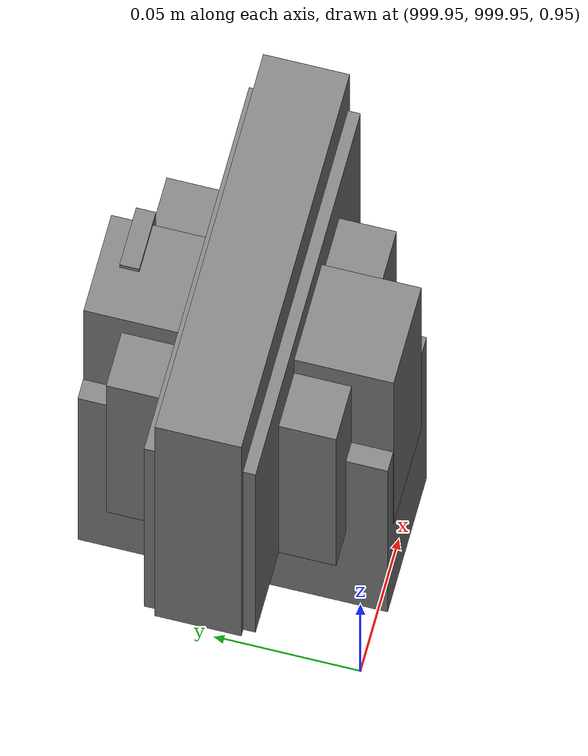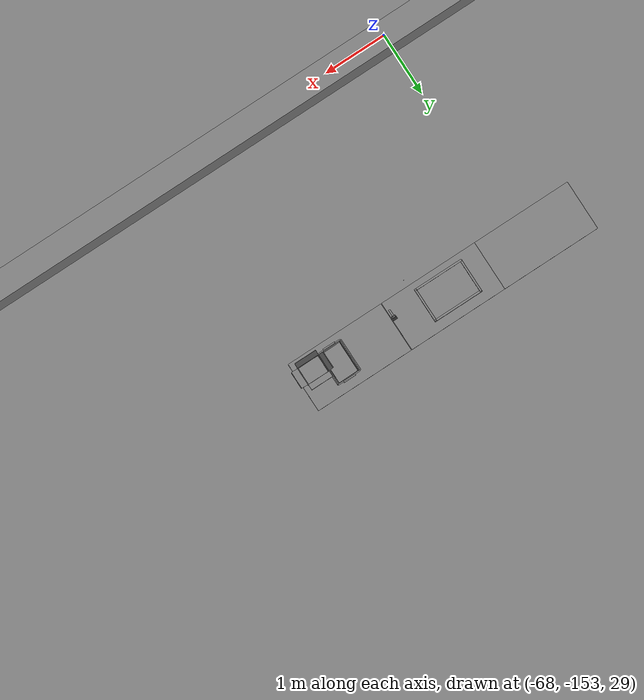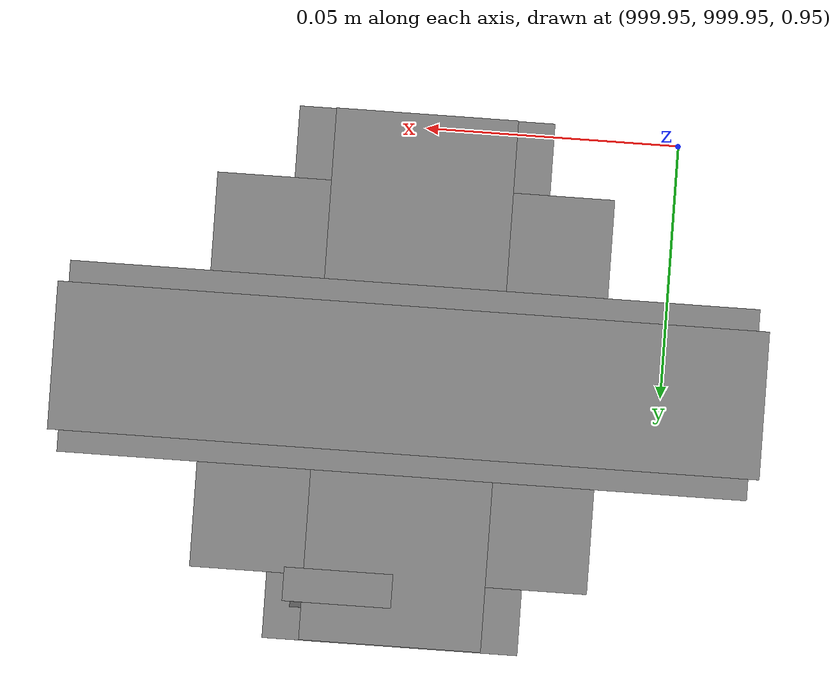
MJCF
<mujoco>
    <option gravity="0.000000000 0.000000000 -9.810000420" timestep="0.0049999999" integrator="implicitfast" density="1.225" viscosity="1.8000001e-05" noslip_iterations="10" iterations="100" sdf_iterations="50">
        <flag multiccd="disable"/>
    </option>
    <size memory="1000M"/>
    <compiler coordinate="local"/>
    <worldbody>
        <light cutoff="30" pos="0 1 1" dir="0 -1 -2"/>
        <light cutoff="30" pos="0 -1 1" dir="0 1 -2"/>
        <body pos="-64.866622925 -149.383972168 30.183746338" euler="89.999984741 89.999946594 0.000000000" name="openloong_gripper_2f85_fix_base_usda_bluebox_01">
            <geom contype="1" conaffinity="1" density="1000" type="box" material="" rgba="0.500000000 0.500000000 0.500000000 1.000000000" solimp="0.899999976 0.949999988 0.001000000" friction="1.000000000 0.005000000 0.000100000" solref="0.020000000 1.000000000" margin="0" condim="3" group="0" pos="0.276580811 0.187225342 0.000068665" quat="0.707106948 0.000077471 0.707106352 0.000077486" size="0.100000001 0.057999998 0.010000000" name="openloong_gripper_2f85_fix_base_usda_geom_3656720E_4E70_47D4_BEDA_C9CD9E4C0865"/>
            <geom contype="1" conaffinity="1" density="1000" type="box" material="" rgba="0.500000000 0.500000000 0.500000000 1.000000000" solimp="0.899999976 0.949999988 0.001000000" friction="1.000000000 0.005000000 0.000100000" solref="0.020000000 1.000000000" margin="0" condim="3" group="0" pos="0.000000000 0.002883911 0.000000000" quat="0.999999881 0.000000000 0.000000000 0.000000000" size="0.254000008 0.003000000 0.172000006" name="openloong_gripper_2f85_fix_base_usda_geom_C48767EE_28CB_49A3_A013_566FD0B0BB4A"/>
            <geom contype="1" conaffinity="1" density="1000" type="box" material="" rgba="0.500000000 0.500000000 0.500000000 1.000000000" solimp="0.899999976 0.949999988 0.001000000" friction="1.000000000 0.005000000 0.000100000" solref="0.020000000 1.000000000" margin="0" condim="3" group="0" pos="0.000000000 0.124874115 0.173484802" quat="0.999796331 0.020176515 -0.000000015 0.000000030" size="0.259999990 0.119999997 0.007000000" name="openloong_gripper_2f85_fix_base_usda_geom_BB47C070_CF74_4C02_940C_DC0D41C4C824"/>
            <geom contype="1" conaffinity="1" density="1000" type="box" material="" rgba="0.500000000 0.500000000 0.500000000 1.000000000" solimp="0.899999976 0.949999988 0.001000000" friction="1.000000000 0.005000000 0.000100000" solref="0.020000000 1.000000000" margin="0" condim="3" group="0" pos="0.000000000 0.124874115 -0.173469543" quat="0.999796331 -0.020176545 -0.000000015 0.000000000" size="0.259999990 0.119999997 0.007000000" name="openloong_gripper_2f85_fix_base_usda_geom_BB486E4A_A57A_4532_B49C_99A2ABAAD3CC"/>
            <geom contype="1" conaffinity="1" density="1000" type="box" material="" rgba="0.500000000 0.500000000 0.500000000 1.000000000" solimp="0.899999976 0.949999988 0.001000000" friction="1.000000000 0.005000000 0.000100000" solref="0.020000000 1.000000000" margin="0" condim="3" group="0" pos="0.000000000 0.214008331 0.188980103" quat="0.999912977 0.013176724 0.000000015 0.000000000" size="0.259999990 0.029999999 0.012500000" name="openloong_gripper_2f85_fix_base_usda_geom_55D2B8F2_BF2E_4B14_B175_363BF109DEED"/>
            <geom contype="1" conaffinity="1" density="1000" type="box" material="" rgba="0.500000000 0.500000000 0.500000000 1.000000000" solimp="0.899999976 0.949999988 0.001000000" friction="1.000000000 0.005000000 0.000100000" solref="0.020000000 1.000000000" margin="0" condim="3" group="0" pos="-0.258361816 0.125289917 0.001876831" quat="0.702796936 -0.020792112 0.710783124 0.020769298" size="0.189999998 0.119999997 0.009000000" name="openloong_gripper_2f85_fix_base_usda_geom_6F0A9163_9BC7_443F_B5E5_DA86D45EE46B"/>
            <geom contype="1" conaffinity="1" density="1000" type="box" material="" rgba="0.500000000 0.500000000 0.500000000 1.000000000" solimp="0.899999976 0.949999988 0.001000000" friction="1.000000000 0.005000000 0.000100000" solref="0.020000000 1.000000000" margin="0" condim="3" group="0" pos="0.000000000 0.214008331 -0.188980103" quat="0.999912977 -0.013176769 0.000000030 0.000000015" size="0.259999990 0.029999999 0.012500000" name="openloong_gripper_2f85_fix_base_usda_geom_96574CDE_A168_4DE8_8970_2569F2B0D3EC"/>
            <geom contype="1" conaffinity="1" density="1000" type="box" material="" rgba="0.500000000 0.500000000 0.500000000 1.000000000" solimp="0.899999976 0.949999988 0.001000000" friction="1.000000000 0.005000000 0.000100000" solref="0.020000000 1.000000000" margin="0" condim="3" group="0" pos="-0.276611328 0.187225342 0.000068665" quat="0.707106650 0.000077441 0.707106709 0.000077456" size="0.100000001 0.057999998 0.010000000" name="openloong_gripper_2f85_fix_base_usda_geom_0E9D8E10_FFA2_4ECC_A55E_A3E9384ED143"/>
            <geom contype="1" conaffinity="1" density="1000" type="box" material="" rgba="0.500000000 0.500000000 0.500000000 1.000000000" solimp="0.899999976 0.949999988 0.001000000" friction="1.000000000 0.005000000 0.000100000" solref="0.020000000 1.000000000" margin="0" condim="3" group="0" pos="0.258331299 0.125289917 0.001876831" quat="0.702851415 0.018856421 0.710823774 -0.019329369" size="0.189999998 0.119999997 0.009000000" name="openloong_gripper_2f85_fix_base_usda_geom_542691D7_710B_438B_A57E_1D70E56CEDA4"/>
            <freejoint name="openloong_gripper_2f85_fix_base_usda_bluebox_01_joint"/>
            <site size="0.005000000 0.005000000 0.005000000" rgba="0.500000000 0.500000000 0.500000000 1.000000000" pos="0.000000000 0.000000000 0.000000000" quat="0.999961913 0.008726534 0.000000000 0.000000000" group="0" type="sphere" name="openloong_gripper_2f85_fix_base_usda_bluebox_01site"/>
        </body>
        <body pos="-64.496299744 -149.491867065 30.235729218" euler="0.000000000 0.000000000 89.999946594" name="openloong_gripper_2f85_fix_base_usda_cardboardbox_01">
            <geom contype="1" conaffinity="1" density="1000" type="box" material="" rgba="0.500000000 0.500000000 0.500000000 1.000000000" solimp="0.899999976 0.949999988 0.001000000" friction="1.000000000 0.005000000 0.000100000" solref="0.020000000 1.000000000" margin="0" condim="3" group="0" pos="-0.003166199 -0.004086494 0.005052090" quat="1.000000000 0.000000000 0.000000000 0.000000000" size="0.142499998 0.177500010 0.005000000" name="openloong_gripper_2f85_fix_base_usda_geom_D64E11F9_C4B6_4525_A474_87AAB6CED257"/>
            <geom contype="1" conaffinity="1" density="1000" type="box" material="" rgba="0.500000000 0.500000000 0.500000000 1.000000000" solimp="0.899999976 0.949999988 0.001000000" friction="1.000000000 0.005000000 0.000100000" solref="0.020000000 1.000000000" margin="0" condim="3" group="0" pos="-0.003166199 0.170316696 0.150570869" quat="1.000000000 0.000000000 0.000000000 0.000000000" size="0.142499998 0.005000000 0.149999991" name="openloong_gripper_2f85_fix_base_usda_geom_16D60688_11A0_47AA_B7A3_7B87427625C3"/>
            <geom contype="1" conaffinity="1" density="1000" type="box" material="" rgba="0.500000000 0.500000000 0.500000000 1.000000000" solimp="0.899999976 0.949999988 0.001000000" friction="1.000000000 0.005000000 0.000100000" solref="0.020000000 1.000000000" margin="0" condim="3" group="0" pos="-0.147399902 -0.005307198 0.150570869" quat="1.000000000 0.000000000 0.000000000 0.000000000" size="0.005000000 0.177500010 0.149999991" name="openloong_gripper_2f85_fix_base_usda_geom_5BD20162_D497_43F9_94CE_22918DD7FD43"/>
            <geom contype="1" conaffinity="1" density="1000" type="box" material="" rgba="0.500000000 0.500000000 0.500000000 1.000000000" solimp="0.899999976 0.949999988 0.001000000" friction="1.000000000 0.005000000 0.000100000" solref="0.020000000 1.000000000" margin="0" condim="3" group="0" pos="0.140275955 -0.005307198 0.150570869" quat="1.000000000 0.000000000 0.000000000 0.000000000" size="0.005000000 0.177500010 0.149999991" name="openloong_gripper_2f85_fix_base_usda_geom_001D366D_980A_46B1_909C_0B12B1DB93C9"/>
            <geom contype="1" conaffinity="1" density="1000" type="box" material="" rgba="0.500000000 0.500000000 0.500000000 1.000000000" solimp="0.899999976 0.949999988 0.001000000" friction="1.000000000 0.005000000 0.000100000" solref="0.020000000 1.000000000" margin="0" condim="3" group="0" pos="-0.003166199 -0.181550980 0.150570869" quat="1.000000000 0.000000000 0.000000000 0.000000000" size="0.142499998 0.005000000 0.149999991" name="openloong_gripper_2f85_fix_base_usda_geom_E2BBE8AB_9DB4_4876_9332_72B901B94489"/>
            <freejoint name="openloong_gripper_2f85_fix_base_usda_cardboardbox_01_joint"/>
            <site size="0.005000000 0.005000000 0.005000000" rgba="0.500000000 0.500000000 0.500000000 1.000000000" pos="0.000000000 0.000000000 0.000000000" quat="0.999961913 0.008726535 0.000000000 0.000000000" group="0" type="sphere" name="openloong_gripper_2f85_fix_base_usda_site_F0BBA40C_0F1C_4FF2_8E18_98178983EBE8"/>
            <body pos="0.139160156 -0.004048347 0.301930904" euler="-179.999954224 49.383502960 179.999954224" name="openloong_gripper_2f85_fix_base_usda_A1_006">
                <geom contype="1" conaffinity="1" density="1000" type="box" material="" rgba="0.500000000 0.500000000 0.500000000 1.000000000" solimp="0.899999976 0.949999988 0.001000000" friction="1.000000000 0.005000000 0.000100000" solref="0.020000000 1.000000000" margin="0" condim="3" group="0" pos="-0.071587563 0.000009537 0.001745224" quat="0.999999881 0.000000000 0.000000000 0.000000000" size="0.071249999 0.179999992 0.002500000" name="openloong_gripper_2f85_fix_base_usda_geom_3E4AB113_66EB_4C0A_B791_3D040BFFDD9B"/>
                <joint armature="0" stiffness="0.07" damping="0.0099999998" axis="0.000000 1.000000 0.000000" type="hinge" name="openloong_gripper_2f85_fix_base_usda_A1_006"/>
            </body>
            <body pos="-0.145902634 -0.004086494 0.301938057" euler="-180.000000000 -60.000011444 -180.000000000" name="openloong_gripper_2f85_fix_base_usda_A2_006">
                <geom contype="1" conaffinity="1" density="1000" type="box" material="" rgba="0.500000000 0.500000000 0.500000000 1.000000000" solimp="0.899999976 0.949999988 0.001000000" friction="1.000000000 0.005000000 0.000100000" solref="0.020000000 1.000000000" margin="0" condim="3" group="0" pos="0.071268082 0.000009537 0.002717972" quat="0.000002921 0.000000000 -0.000000030 0.999999881" size="0.071249999 0.179999992 0.002500000" name="openloong_gripper_2f85_fix_base_usda_geom_401F5C48_DA76_494D_BB4B_E149826E9B47"/>
                <joint armature="0" stiffness="0.07" damping="0.0099999998" axis="0.000000 1.000000 0.000000" type="hinge" name="openloong_gripper_2f85_fix_base_usda_A2_006"/>
            </body>
            <body pos="-0.003385544 0.175991058 0.301930904" euler="-125.858116150 -0.000004561 0.000002331" name="openloong_gripper_2f85_fix_base_usda_B2_006">
                <geom contype="1" conaffinity="1" density="1000" type="box" material="" rgba="0.500000000 0.500000000 0.500000000 1.000000000" solimp="0.899999976 0.949999988 0.001000000" friction="1.000000000 0.005000000 0.000100000" solref="0.020000000 1.000000000" margin="0" condim="3" group="0" pos="0.000009537 -0.070939064 -0.002470016" quat="0.999614120 0.027776197 -0.000000015 0.000000030" size="0.137500003 0.064999998 0.005000000" name="openloong_gripper_2f85_fix_base_usda_geom_92F28FD6_B816_4067_9CB0_0AFE4B36C5AA"/>
                <joint armature="0" stiffness="0.07" damping="0.0099999998" axis="1.000000 0.000000 0.000000" type="hinge" name="openloong_gripper_2f85_fix_base_usda_B2_006"/>
            </body>
            <body pos="-0.003385544 -0.184140205 0.301938057" euler="147.805557251 0.000000000 0.000000000" name="openloong_gripper_2f85_fix_base_usda_B1_006">
                <geom contype="1" conaffinity="1" density="1000" type="box" material="" rgba="0.500000000 0.500000000 0.500000000 1.000000000" solimp="0.899999976 0.949999988 0.001000000" friction="1.000000000 0.005000000 0.000100000" solref="0.020000000 1.000000000" margin="0" condim="3" group="0" pos="-0.000028610 0.070202351 -0.002703667" quat="0.999614179 -0.027776167 0.000000000 0.000000000" size="0.137500003 0.064999998 0.005000000" name="openloong_gripper_2f85_fix_base_usda_geom_0F2CD6C8_519F_4BDC_A709_CDD50EE52A23"/>
                <joint armature="0" stiffness="0.07" damping="0.0099999998" axis="1.000000 0.000000 0.000000" type="hinge" name="openloong_gripper_2f85_fix_base_usda_B1_006"/>
            </body>
        </body>
        <body pos="-65.882858276 -149.481979370 30.229999542" euler="-64.487716675 0.000000000 0.000000000" name="openloong_gripper_2f85_fix_base_usda_Barcode">
            <geom contype="1" conaffinity="1" density="1000" type="box" material="" rgba="0.500000000 0.500000000 0.500000000 1.000000000" solimp="0.899999976 0.949999988 0.001000000" friction="1.000000000 0.005000000 0.000100000" solref="0.020000000 1.000000000" margin="0" condim="3" group="0" pos="0.000000000 0.013038635 0.001419067" quat="0.000000000 0.000000000 0.000000000 1.000000119" size="0.034000002 0.010000000 0.017999999" name="openloong_gripper_2f85_fix_base_usda_geom_6E98B946_5262_445A_9AF4_7CBE847684A8"/>
            <geom contype="1" conaffinity="1" density="1000" type="box" material="" rgba="0.500000000 0.500000000 0.500000000 1.000000000" solimp="0.899999976 0.949999988 0.001000000" friction="1.000000000 0.005000000 0.000100000" solref="0.020000000 1.000000000" margin="0" condim="3" group="0" pos="0.000000000 -0.035301208 -0.007095337" quat="0.000000000 0.000000000 -0.043619365 0.999048233" size="0.028999999 0.010000000 0.020000000" name="openloong_gripper_2f85_fix_base_usda_geom_9CD2F0DD_4394_4F6C_BC84_D016BBA3245A"/>
            <geom contype="1" conaffinity="1" density="1000" type="box" material="" rgba="0.500000000 0.500000000 0.500000000 1.000000000" solimp="0.899999976 0.949999988 0.001000000" friction="1.000000000 0.005000000 0.000100000" solref="0.020000000 1.000000000" margin="0" condim="3" group="0" pos="0.000000000 -0.043411255 -0.011749268" quat="0.922262907 0.386563420 0.000000000 0.000000000" size="0.026000001 0.010000000 0.020000000" name="openloong_gripper_2f85_fix_base_usda_geom_E50351BC_9163_4773_95E2_0BE641005A19"/>
            <geom contype="1" conaffinity="1" density="1000" type="box" material="" rgba="0.500000000 0.500000000 0.500000000 1.000000000" solimp="0.899999976 0.949999988 0.001000000" friction="1.000000000 0.005000000 0.000100000" solref="0.020000000 1.000000000" margin="0" condim="3" group="0" pos="0.000000000 -0.016967773 -0.031860352" quat="0.000000000 0.000000000 0.000000000 1.000000119" size="0.008000000 0.010000000 0.013000000" name="openloong_gripper_2f85_fix_base_usda_geom_9C28B1AB_8EE5_438A_A10A_DFE797434152"/>
            <geom contype="1" conaffinity="1" density="1000" type="box" material="" rgba="0.500000000 0.500000000 0.500000000 1.000000000" solimp="0.899999976 0.949999988 0.001000000" friction="1.000000000 0.005000000 0.000100000" solref="0.020000000 1.000000000" margin="0" condim="3" group="0" pos="0.000000000 -0.001869202 0.000312805" quat="0.953716993 0.300705761 0.000000000 0.000000000" size="0.032000002 0.010000000 0.018999999" name="openloong_gripper_2f85_fix_base_usda_geom_87F70831_9DBC_495C_AA63_A4051AB0F3A6"/>
            <geom contype="1" conaffinity="1" density="1000" type="box" material="" rgba="0.500000000 0.500000000 0.500000000 1.000000000" solimp="0.899999976 0.949999988 0.001000000" friction="1.000000000 0.005000000 0.000100000" solref="0.020000000 1.000000000" margin="0" condim="3" group="0" pos="0.000000000 -0.019531250 -0.003173828" quat="0.953716993 0.300705761 0.000000000 0.000000000" size="0.030999999 0.010000000 0.020000000" name="openloong_gripper_2f85_fix_base_usda_geom_5B46320F_AB4F_40ED_821D_12927FDB771A"/>
            <geom contype="1" conaffinity="1" density="1000" type="box" material="" rgba="0.500000000 0.500000000 0.500000000 1.000000000" solimp="0.899999976 0.949999988 0.001000000" friction="1.000000000 0.005000000 0.000100000" solref="0.020000000 1.000000000" margin="0" condim="3" group="0" pos="0.000000000 -0.035301208 -0.007095337" quat="0.953716993 0.300705761 0.000000000 0.000000000" size="0.028999999 0.010000000 0.020000000" name="openloong_gripper_2f85_fix_base_usda_geom_C5598A6F_F15A_42DA_B167_1EE9CF8F5483"/>
            <geom contype="1" conaffinity="1" density="1000" type="box" material="" rgba="0.500000000 0.500000000 0.500000000 1.000000000" solimp="0.899999976 0.949999988 0.001000000" friction="1.000000000 0.005000000 0.000100000" solref="0.020000000 1.000000000" margin="0" condim="3" group="0" pos="0.000000000 -0.042617798 -0.071121216" quat="0.000000000 0.000000000 0.000000000 1.000000119" size="0.013000000 0.021000000 0.059999999" name="openloong_gripper_2f85_fix_base_usda_geom_DB935773_0A9D_421A_9F7F_24ACDDBEBFD1"/>
            <freejoint name="openloong_gripper_2f85_fix_base_usda_Barcode_joint"/>
            <site size="0.005000000 0.005000000 0.005000000" rgba="0.500000000 0.500000000 0.500000000 1.000000000" pos="0.000000000 0.000000000 0.000000000" quat="1.000000000 0.000000000 0.000000000 0.000000000" group="0" type="sphere" name="openloong_gripper_2f85_fix_base_usda_Barcode_site"/>
        </body>
        <body pos="-66.745018005 -149.392349243 30.184000015" euler="0.000000000 0.000000000 89.999946594" name="[22329957847453]_Basket_01">
            <geom contype="1" conaffinity="1" density="1000" type="box" material="" rgba="0.500000000 0.500000000 0.500000000 1.000000000" solimp="0.899999976 0.949999988 0.001000000" friction="1.000000000 0.005000000 0.000100000" solref="0.020000000 1.000000000" margin="0" condim="3" group="0" pos="-0.052425385 0.389207840 0.089787483" quat="0.707107008 0.000000000 0.000000000 0.707106411" size="0.014249999 0.014249999 0.059999999" name="[22329957847453]_geom_D71046F8_3169_4806_9195_769DEAF79A85"/>
            <geom contype="1" conaffinity="1" density="1000" type="box" material="" rgba="0.500000000 0.500000000 0.500000000 1.000000000" solimp="0.899999976 0.949999988 0.001000000" friction="1.000000000 0.005000000 0.000100000" solref="0.020000000 1.000000000" margin="0" condim="3" group="0" pos="0.264015198 -0.133043289 0.089787483" quat="0.707107008 0.000000000 0.000000000 0.707106411" size="0.014249999 0.014249999 0.059999999" name="[22329957847453]_geom_1BBA4C01_3915_4EE3_BF33_B4991EF7F0F5"/>
            <geom contype="1" conaffinity="1" density="1000" type="box" material="" rgba="0.500000000 0.500000000 0.500000000 1.000000000" solimp="0.899999976 0.949999988 0.001000000" friction="1.000000000 0.005000000 0.000100000" solref="0.020000000 1.000000000" margin="0" condim="3" group="0" pos="-0.264015198 -0.265548706 0.089793205" quat="0.707107008 0.000000000 0.000000000 0.707106411" size="0.014249999 0.014249999 0.059999999" name="[22329957847453]_geom_BAA58141_A290_47DF_8756_853765A69231"/>
            <geom contype="1" conaffinity="1" density="1000" type="box" material="" rgba="0.500000000 0.500000000 0.500000000 1.000000000" solimp="0.899999976 0.949999988 0.001000000" friction="1.000000000 0.005000000 0.000100000" solref="0.020000000 1.000000000" margin="0" condim="3" group="0" pos="-0.160263062 -0.389322281 0.089793205" quat="0.707107008 0.000000000 0.000000000 0.707106411" size="0.014249999 0.014249999 0.059999999" name="[22329957847453]_geom_2A439860_3787_4141_8D14_3050A7A2123C"/>
            <geom contype="1" conaffinity="1" density="1000" type="box" material="" rgba="0.500000000 0.500000000 0.500000000 1.000000000" solimp="0.899999976 0.949999988 0.001000000" friction="1.000000000 0.005000000 0.000100000" solref="0.020000000 1.000000000" margin="0" condim="3" group="0" pos="0.162265778 -0.389322281 0.089787483" quat="0.707107008 0.000000000 0.000000000 0.707106411" size="0.014249999 0.014249999 0.059999999" name="[22329957847453]_geom_72C7E7F3_A4E1_4997_B3E7_BAEFCF736923"/>
            <geom contype="1" conaffinity="1" density="1000" type="box" material="" rgba="0.500000000 0.500000000 0.500000000 1.000000000" solimp="0.899999976 0.949999988 0.001000000" friction="1.000000000 0.005000000 0.000100000" solref="0.020000000 1.000000000" margin="0" condim="3" group="0" pos="0.264015198 0.389207840 0.089787483" quat="0.707107008 0.000000000 0.000000000 0.707106411" size="0.014249999 0.014249999 0.059999999" name="[22329957847453]_geom_CD1C1C17_C5F4_455A_B5CC_70C199CC350A"/>
            <geom contype="1" conaffinity="1" density="1000" type="box" material="" rgba="0.500000000 0.500000000 0.500000000 1.000000000" solimp="0.899999976 0.949999988 0.001000000" friction="1.000000000 0.005000000 0.000100000" solref="0.020000000 1.000000000" margin="0" condim="3" group="0" pos="-0.264015198 -0.133043289 0.089793205" quat="0.707107008 0.000000000 0.000000000 0.707106411" size="0.014249999 0.014249999 0.059999999" name="[22329957847453]_geom_B929EB58_92AC_4511_B5E8_14BA9360E715"/>
            <geom contype="1" conaffinity="1" density="1000" type="box" material="" rgba="0.500000000 0.500000000 0.500000000 1.000000000" solimp="0.899999976 0.949999988 0.001000000" friction="1.000000000 0.005000000 0.000100000" solref="0.020000000 1.000000000" margin="0" condim="3" group="0" pos="-0.264026642 0.269256592 0.089793205" quat="0.707107008 0.000000000 0.000000000 0.707106411" size="0.014249999 0.014249999 0.059999999" name="[22329957847453]_geom_7FBED822_E2F7_481B_90EB_7200EA3E372A"/>
            <geom contype="1" conaffinity="1" density="1000" type="box" material="" rgba="0.500000000 0.500000000 0.500000000 1.000000000" solimp="0.899999976 0.949999988 0.001000000" friction="1.000000000 0.005000000 0.000100000" solref="0.020000000 1.000000000" margin="0" condim="3" group="0" pos="0.054462433 0.389207840 0.089787483" quat="0.707107008 0.000000000 0.000000000 0.707106411" size="0.014249999 0.014249999 0.059999999" name="[22329957847453]_geom_A04F2F97_001E_485B_8CD0_530CB4BD56E1"/>
            <geom contype="1" conaffinity="1" density="1000" type="box" material="" rgba="0.500000000 0.500000000 0.500000000 1.000000000" solimp="0.899999976 0.949999988 0.001000000" friction="1.000000000 0.005000000 0.000100000" solref="0.020000000 1.000000000" margin="0" condim="3" group="0" pos="0.054462433 -0.389322281 0.089787483" quat="0.707107008 0.000000000 0.000000000 0.707106411" size="0.014249999 0.014249999 0.059999999" name="[22329957847453]_geom_5A9BA8D4_D843_40ED_9C2B_950941C8A0A6"/>
            <geom contype="1" conaffinity="1" density="1000" type="box" material="" rgba="0.500000000 0.500000000 0.500000000 1.000000000" solimp="0.899999976 0.949999988 0.001000000" friction="1.000000000 0.005000000 0.000100000" solref="0.020000000 1.000000000" margin="0" condim="3" group="0" pos="0.264015198 0.269256592 0.089793205" quat="0.707107008 0.000000000 0.000000000 0.707106411" size="0.014249999 0.014249999 0.059999999" name="[22329957847453]_geom_80C15291_B83A_4CD6_A00F_C0D6692F2518"/>
            <geom contype="1" conaffinity="1" density="1000" type="box" material="" rgba="0.500000000 0.500000000 0.500000000 1.000000000" solimp="0.899999976 0.949999988 0.001000000" friction="1.000000000 0.005000000 0.000100000" solref="0.020000000 1.000000000" margin="0" condim="3" group="0" pos="0.264015198 -0.389322281 0.089787483" quat="0.707107008 0.000000000 0.000000000 0.707106411" size="0.014249999 0.014249999 0.059999999" name="[22329957847453]_geom_FC063C30_CF62_439D_A7F8_3BF820080F66"/>
            <geom contype="1" conaffinity="1" density="1000" type="box" material="" rgba="0.500000000 0.500000000 0.500000000 1.000000000" solimp="0.899999976 0.949999988 0.001000000" friction="1.000000000 0.005000000 0.000100000" solref="0.020000000 1.000000000" margin="0" condim="3" group="0" pos="0.000000000 0.000000000 0.015998840" quat="0.707107008 0.000000000 0.000000000 0.707106411" size="0.403499991 0.279000014 0.015750000" name="[22329957847453]_geom_B1B36A88_B1C2_431F_B836_E65EF7B4C824"/>
            <geom contype="1" conaffinity="1" density="1000" type="box" material="" rgba="0.500000000 0.500000000 0.500000000 1.000000000" solimp="0.899999976 0.949999988 0.001000000" friction="1.000000000 0.005000000 0.000100000" solref="0.020000000 1.000000000" margin="0" condim="3" group="0" pos="0.000000000 -0.389476776 0.163619041" quat="0.707107008 0.000000000 0.000000000 0.707106411" size="0.015000000 0.277500004 0.015750000" name="[22329957847453]_geom_2A611FFC_D33D_46DC_A1F5_9B5DD22D9DFA"/>
            <geom contype="1" conaffinity="1" density="1000" type="box" material="" rgba="0.500000000 0.500000000 0.500000000 1.000000000" solimp="0.899999976 0.949999988 0.001000000" friction="1.000000000 0.005000000 0.000100000" solref="0.020000000 1.000000000" margin="0" condim="3" group="0" pos="0.162265778 0.389207840 0.089787483" quat="0.707107008 0.000000000 0.000000000 0.707106411" size="0.014249999 0.014249999 0.059999999" name="[22329957847453]_geom_35ECC938_EBAE_4EBD_93F9_2FD8708F1F5E"/>
            <geom contype="1" conaffinity="1" density="1000" type="box" material="" rgba="0.500000000 0.500000000 0.500000000 1.000000000" solimp="0.899999976 0.949999988 0.001000000" friction="1.000000000 0.005000000 0.000100000" solref="0.020000000 1.000000000" margin="0" condim="3" group="0" pos="0.000000000 0.389471054 0.163619041" quat="0.707107008 0.000000000 0.000000000 0.707106411" size="0.015000000 0.277500004 0.015750000" name="[22329957847453]_geom_400642E4_F0FF_4A1E_AF20_688E2CA73E99"/>
            <geom contype="1" conaffinity="1" density="1000" type="box" material="" rgba="0.500000000 0.500000000 0.500000000 1.000000000" solimp="0.899999976 0.949999988 0.001000000" friction="1.000000000 0.005000000 0.000100000" solref="0.020000000 1.000000000" margin="0" condim="3" group="0" pos="-0.263511658 0.000000000 0.163619041" quat="0.707107008 0.000000000 0.000000000 0.707106411" size="0.403499991 0.015000000 0.015750000" name="[22329957847453]_geom_9C0E5B8C_6531_4F8A_9B56_DF121B21B16E"/>
            <geom contype="1" conaffinity="1" density="1000" type="box" material="" rgba="0.500000000 0.500000000 0.500000000 1.000000000" solimp="0.899999976 0.949999988 0.001000000" friction="1.000000000 0.005000000 0.000100000" solref="0.020000000 1.000000000" margin="0" condim="3" group="0" pos="-0.264015198 0.141334534 0.089793205" quat="0.707107008 0.000000000 0.000000000 0.707106411" size="0.014249999 0.014249999 0.059999999" name="[22329957847453]_geom_3AF5056C_133F_4281_BC45_267979E94674"/>
            <geom contype="1" conaffinity="1" density="1000" type="box" material="" rgba="0.500000000 0.500000000 0.500000000 1.000000000" solimp="0.899999976 0.949999988 0.001000000" friction="1.000000000 0.005000000 0.000100000" solref="0.020000000 1.000000000" margin="0" condim="3" group="0" pos="0.264015198 -0.265548706 0.089787483" quat="0.707107008 0.000000000 0.000000000 0.707106411" size="0.014249999 0.014249999 0.059999999" name="[22329957847453]_geom_257DDED5_3C91_46AB_A213_E01B910F700E"/>
            <geom contype="1" conaffinity="1" density="1000" type="box" material="" rgba="0.500000000 0.500000000 0.500000000 1.000000000" solimp="0.899999976 0.949999988 0.001000000" friction="1.000000000 0.005000000 0.000100000" solref="0.020000000 1.000000000" margin="0" condim="3" group="0" pos="-0.160263062 0.389207840 0.089787483" quat="0.707107008 0.000000000 0.000000000 0.707106411" size="0.014249999 0.014249999 0.059999999" name="[22329957847453]_geom_548FD626_FD7F_48C8_86C3_FB220AFEE060"/>
            <geom contype="1" conaffinity="1" density="1000" type="box" material="" rgba="0.500000000 0.500000000 0.500000000 1.000000000" solimp="0.899999976 0.949999988 0.001000000" friction="1.000000000 0.005000000 0.000100000" solref="0.020000000 1.000000000" margin="0" condim="3" group="0" pos="-0.052425385 -0.389322281 0.089787483" quat="0.707107008 0.000000000 0.000000000 0.707106411" size="0.014249999 0.014249999 0.059999999" name="[22329957847453]_geom_F58E4571_FA1F_45F8_B38D_5E974FD8F596"/>
            <geom contype="1" conaffinity="1" density="1000" type="box" material="" rgba="0.500000000 0.500000000 0.500000000 1.000000000" solimp="0.899999976 0.949999988 0.001000000" friction="1.000000000 0.005000000 0.000100000" solref="0.020000000 1.000000000" margin="0" condim="3" group="0" pos="-0.264026642 -0.389322281 0.089793205" quat="0.707107008 0.000000000 0.000000000 0.707106411" size="0.014249999 0.014249999 0.059999999" name="[22329957847453]_geom_B407C432_B016_44BC_B9A5_D1BDE872E09E"/>
            <geom contype="1" conaffinity="1" density="1000" type="box" material="" rgba="0.500000000 0.500000000 0.500000000 1.000000000" solimp="0.899999976 0.949999988 0.001000000" friction="1.000000000 0.005000000 0.000100000" solref="0.020000000 1.000000000" margin="0" condim="3" group="0" pos="0.264015198 0.141334534 0.089787483" quat="0.707107008 0.000000000 0.000000000 0.707106411" size="0.014249999 0.014249999 0.059999999" name="[22329957847453]_geom_D50D20B0_CE55_4EC3_944F_A40B0BA042D6"/>
            <geom contype="1" conaffinity="1" density="1000" type="box" material="" rgba="0.500000000 0.500000000 0.500000000 1.000000000" solimp="0.899999976 0.949999988 0.001000000" friction="1.000000000 0.005000000 0.000100000" solref="0.020000000 1.000000000" margin="0" condim="3" group="0" pos="-0.264015198 0.389207840 0.089793205" quat="0.707107008 0.000000000 0.000000000 0.707106411" size="0.014249999 0.014249999 0.059999999" name="[22329957847453]_geom_6C4F3416_63DD_45C5_8B89_DAB40D2EC3D6"/>
            <geom contype="1" conaffinity="1" density="1000" type="box" material="" rgba="0.500000000 0.500000000 0.500000000 1.000000000" solimp="0.899999976 0.949999988 0.001000000" friction="1.000000000 0.005000000 0.000100000" solref="0.020000000 1.000000000" margin="0" condim="3" group="0" pos="0.264015198 0.004480362 0.089787483" quat="0.707107008 0.000000000 0.000000000 0.707106411" size="0.014249999 0.014249999 0.059999999" name="[22329957847453]_geom_E019AD74_C95D_4E61_AD9C_84A61A1CAD51"/>
            <geom contype="1" conaffinity="1" density="1000" type="box" material="" rgba="0.500000000 0.500000000 0.500000000 1.000000000" solimp="0.899999976 0.949999988 0.001000000" friction="1.000000000 0.005000000 0.000100000" solref="0.020000000 1.000000000" margin="0" condim="3" group="0" pos="0.263694763 -0.000011444 0.163619041" quat="0.707107008 0.000000000 0.000000000 0.707106411" size="0.403499991 0.015000000 0.015750000" name="[22329957847453]_geom_C80A4150_FD9D_44BB_8CBE_83375AAFF8E4"/>
            <geom contype="1" conaffinity="1" density="1000" type="box" material="" rgba="0.500000000 0.500000000 0.500000000 1.000000000" solimp="0.899999976 0.949999988 0.001000000" friction="1.000000000 0.005000000 0.000100000" solref="0.020000000 1.000000000" margin="0" condim="3" group="0" pos="-0.264015198 0.004480362 0.089793205" quat="0.707107008 0.000000000 0.000000000 0.707106411" size="0.014249999 0.014249999 0.059999999" name="[22329957847453]_geom_4D85F191_516C_4B43_8105_FB5D67DA3017"/>
            <freejoint name="[22329957847453]_joint_B2C695ED_E61E_47AC_B11C_04456140BCC4"/>
        </body>
        <body pos="0.000000000 0.000000000 0.000000000" euler="0.000000000 0.000000000 0.000000000" name="Static Objects_Static Objects">
            <geom contype="1" conaffinity="1" density="1000" type="box" material="" rgba="0.500000000 0.500000000 0.500000000 1.000000000" solimp="0.899999976 0.949999988 0.001000000" friction="1.000000000 0.005000000 0.000100000" solref="0.020000000 1.000000000" margin="0" condim="3" group="0" pos="-67.544113159 -149.365814209 29.727830887" quat="0.500000417 0.499999970 0.499999553 0.499999970" size="0.381000012 0.319999993 0.041000001" name="Static Objects_geom_292D6DDD_CE3E_41E0_AFA6_E2E56C6ED8F4"/>
            <geom contype="1" conaffinity="1" density="1000" type="box" material="" rgba="0.500000000 0.500000000 0.500000000 1.000000000" solimp="0.899999976 0.949999988 0.001000000" friction="1.000000000 0.005000000 0.000100000" solref="0.020000000 1.000000000" margin="0" condim="3" group="0" pos="-68.239501953 -149.365814209 30.086868286" quat="0.500000417 0.499999970 0.499999553 0.499999970" size="0.370999992 0.039500002 0.745000005" name="Static Objects_geom_8BEB9A6A_8878_44BE_B604_91B91547A4C7"/>
            <geom contype="1" conaffinity="1" density="1000" type="box" material="" rgba="0.500000000 0.500000000 0.500000000 1.000000000" solimp="0.899999976 0.949999988 0.001000000" friction="1.000000000 0.005000000 0.000100000" solref="0.020000000 1.000000000" margin="0" condim="3" group="0" pos="-68.239501953 -149.365814209 30.147235870" quat="0.500000417 0.499999970 0.499999553 0.499999970" size="0.400000006 0.022000000 0.800000012" name="Static Objects_geom_91BB2442_5839_4473_9EA2_1DD54C670C16"/>
            <geom contype="1" conaffinity="1" density="1000" type="box" material="" rgba="0.500000000 0.500000000 0.500000000 1.000000000" solimp="0.899999976 0.949999988 0.001000000" friction="1.000000000 0.005000000 0.000100000" solref="0.020000000 1.000000000" margin="0" condim="3" group="0" pos="-68.934890747 -149.365814209 29.727830887" quat="0.500000417 0.499999970 0.499999553 0.499999970" size="0.381000012 0.319999993 0.041000001" name="Static Objects_geom_04A19B5F_4C63_4A33_8070_4B62C3C02346"/>
            <geom contype="1" conaffinity="1" density="1000" type="box" material="" rgba="0.500000000 0.500000000 0.500000000 1.000000000" solimp="0.899999976 0.949999988 0.001000000" friction="1.000000000 0.005000000 0.000100000" solref="0.020000000 1.000000000" margin="0" condim="3" group="0" pos="-68.239501953 -149.365814209 29.561563492" quat="0.500000417 0.499999970 0.499999553 0.499999970" size="0.020000000 0.022000000 0.660000026" name="Static Objects_geom_487E54C2_15B5_4C2C_A136_702E69ECD1C1"/>
            <geom contype="1" conaffinity="1" density="1000" type="box" material="" rgba="0.500000000 0.500000000 0.500000000 1.000000000" solimp="0.899999976 0.949999988 0.001000000" friction="1.000000000 0.005000000 0.000100000" solref="0.020000000 1.000000000" margin="0" condim="3" group="0" pos="-65.945671082 -149.365814209 29.727830887" quat="0.500000417 0.499999970 0.499999553 0.499999970" size="0.381000012 0.319999993 0.041000001" name="Static Objects_geom_5C193C4D_DF61_43BA_93EC_F7CA1A085D96"/>
            <geom contype="1" conaffinity="1" density="1000" type="box" material="" rgba="0.500000000 0.500000000 0.500000000 1.000000000" solimp="0.899999976 0.949999988 0.001000000" friction="1.000000000 0.005000000 0.000100000" solref="0.020000000 1.000000000" margin="0" condim="3" group="0" pos="-66.641059875 -149.365814209 30.086868286" quat="0.500000417 0.499999970 0.499999553 0.499999970" size="0.370999992 0.039500002 0.745000005" name="Static Objects_geom_A99B8312_11A1_4C48_AB6C_36DF9A51B699"/>
            <geom contype="1" conaffinity="1" density="1000" type="box" material="" rgba="0.500000000 0.500000000 0.500000000 1.000000000" solimp="0.899999976 0.949999988 0.001000000" friction="1.000000000 0.005000000 0.000100000" solref="0.020000000 1.000000000" margin="0" condim="3" group="0" pos="-66.641059875 -149.365814209 30.147235870" quat="0.500000417 0.499999970 0.499999553 0.499999970" size="0.400000006 0.022000000 0.800000012" name="Static Objects_geom_8A60C180_FF55_4F43_8694_CB40785C20E7"/>
            <geom contype="1" conaffinity="1" density="1000" type="box" material="" rgba="0.500000000 0.500000000 0.500000000 1.000000000" solimp="0.899999976 0.949999988 0.001000000" friction="1.000000000 0.005000000 0.000100000" solref="0.020000000 1.000000000" margin="0" condim="3" group="0" pos="-67.336448669 -149.365814209 29.727830887" quat="0.500000417 0.499999970 0.499999553 0.499999970" size="0.381000012 0.319999993 0.041000001" name="Static Objects_geom_DBB62599_9159_44B7_B4E7_13079FC698C2"/>
            <geom contype="1" conaffinity="1" density="1000" type="box" material="" rgba="0.500000000 0.500000000 0.500000000 1.000000000" solimp="0.899999976 0.949999988 0.001000000" friction="1.000000000 0.005000000 0.000100000" solref="0.020000000 1.000000000" margin="0" condim="3" group="0" pos="-66.641059875 -149.365814209 29.561563492" quat="0.500000417 0.499999970 0.499999553 0.499999970" size="0.020000000 0.022000000 0.660000026" name="Static Objects_geom_74539F11_1261_4747_A753_C7A2B0A0AB85"/>
            <geom contype="1" conaffinity="1" density="1000" type="box" material="" rgba="0.500000000 0.500000000 0.500000000 1.000000000" solimp="0.899999976 0.949999988 0.001000000" friction="1.000000000 0.005000000 0.000100000" solref="0.020000000 1.000000000" margin="0" condim="3" group="0" pos="-64.338577271 -149.365814209 29.727830887" quat="0.500000417 0.499999970 0.499999553 0.499999970" size="0.381000012 0.319999993 0.041000001" name="Static Objects_geom_0D4BE799_BFD3_4030_B824_92B38FB67B98"/>
            <geom contype="1" conaffinity="1" density="1000" type="box" material="" rgba="0.500000000 0.500000000 0.500000000 1.000000000" solimp="0.899999976 0.949999988 0.001000000" friction="1.000000000 0.005000000 0.000100000" solref="0.020000000 1.000000000" margin="0" condim="3" group="0" pos="-65.033966064 -149.365814209 30.086868286" quat="0.500000417 0.499999970 0.499999553 0.499999970" size="0.370999992 0.039500002 0.745000005" name="Static Objects_geom_5F13FDC4_7570_425F_AC17_CB7CC9F015E2"/>
            <geom contype="1" conaffinity="1" density="1000" type="box" material="" rgba="0.500000000 0.500000000 0.500000000 1.000000000" solimp="0.899999976 0.949999988 0.001000000" friction="1.000000000 0.005000000 0.000100000" solref="0.020000000 1.000000000" margin="0" condim="3" group="0" pos="-65.033966064 -149.365814209 30.147235870" quat="0.500000417 0.499999970 0.499999553 0.499999970" size="0.400000006 0.022000000 0.800000012" name="Static Objects_geom_3ABC089D_F4F6_4849_BA31_FF4075FB142B"/>
            <geom contype="1" conaffinity="1" density="1000" type="box" material="" rgba="0.500000000 0.500000000 0.500000000 1.000000000" solimp="0.899999976 0.949999988 0.001000000" friction="1.000000000 0.005000000 0.000100000" solref="0.020000000 1.000000000" margin="0" condim="3" group="0" pos="-65.729354858 -149.365814209 29.727830887" quat="0.500000417 0.499999970 0.499999553 0.499999970" size="0.381000012 0.319999993 0.041000001" name="Static Objects_geom_49869F87_77F0_4653_94C3_A5E04527EB0A"/>
            <geom contype="1" conaffinity="1" density="1000" type="box" material="" rgba="0.500000000 0.500000000 0.500000000 1.000000000" solimp="0.899999976 0.949999988 0.001000000" friction="1.000000000 0.005000000 0.000100000" solref="0.020000000 1.000000000" margin="0" condim="3" group="0" pos="-65.033966064 -149.365814209 29.561563492" quat="0.500000417 0.499999970 0.499999553 0.499999970" size="0.020000000 0.022000000 0.660000026" name="Static Objects_geom_989E0082_0391_42ED_B208_BDC68A09BE19"/>
            <geom contype="1" conaffinity="1" density="1000" type="box" material="" rgba="0.500000000 0.500000000 0.500000000 1.000000000" solimp="0.899999976 0.949999988 0.001000000" friction="1.000000000 0.005000000 0.000100000" solref="0.020000000 1.000000000" margin="0" condim="3" group="0" pos="-61.754566193 -137.853729248 33.906845093" quat="0.707107067 0.000000000 0.000000000 0.707106471" size="0.759999990 0.759999990 4.500000000" name="Static Objects_geom_027E328D_77B7_44EC_83F1_EB3E53DBDB16"/>
            <geom contype="1" conaffinity="1" density="1000" type="box" material="" rgba="0.500000000 0.500000000 0.500000000 1.000000000" solimp="0.899999976 0.949999988 0.001000000" friction="1.000000000 0.005000000 0.000100000" solref="0.020000000 1.000000000" margin="0" condim="3" group="0" pos="-57.511135101 -144.927108765 31.707921982" quat="1.000000000 0.000000000 0.000000000 0.000000000" size="0.200000003 8.000000000 2.299999952" name="Static Objects_geom_B621E53F_BEC1_440E_9415_35AB0F7DF510"/>
            <geom contype="1" conaffinity="1" density="1000" type="box" material="" rgba="0.500000000 0.500000000 0.500000000 1.000000000" solimp="0.899999976 0.949999988 0.001000000" friction="1.000000000 0.005000000 0.000100000" solref="0.020000000 1.000000000" margin="0" condim="3" group="0" pos="-80.517646790 -157.574050903 31.688196182" quat="0.707107067 0.000000000 0.000000000 0.707106471" size="0.600000024 0.600000024 2.299999952" name="Static Objects_geom_969E26B6_3D2F_47DE_AFF3_E52B19F62737"/>
            <geom contype="1" conaffinity="1" density="1000" type="box" material="" rgba="0.500000000 0.500000000 0.500000000 1.000000000" solimp="0.899999976 0.949999988 0.001000000" friction="1.000000000 0.005000000 0.000100000" solref="0.020000000 1.000000000" margin="0" condim="3" group="0" pos="-80.711044312 -147.414932251 31.666158676" quat="1.000000000 0.000000000 0.000000000 0.000000000" size="0.200000003 10.000000000 2.299999952" name="Static Objects_geom_28317A33_B13A_4928_9104_35C0D61ECF2F"/>
            <geom contype="1" conaffinity="1" density="1000" type="box" material="" rgba="0.500000000 0.500000000 0.500000000 1.000000000" solimp="0.899999976 0.949999988 0.001000000" friction="1.000000000 0.005000000 0.000100000" solref="0.020000000 1.000000000" margin="0" condim="3" group="0" pos="-57.687217712 -137.434692383 31.688196182" quat="0.707107067 0.000000000 0.000000000 0.707106471" size="0.600000024 0.600000024 2.299999952" name="Static Objects_geom_3869FAF4_DA77_46C8_8FA7_35F252EFCF77"/>
            <geom contype="1" conaffinity="1" density="1000" type="box" material="" rgba="0.500000000 0.500000000 0.500000000 1.000000000" solimp="0.899999976 0.949999988 0.001000000" friction="1.000000000 0.005000000 0.000100000" solref="0.020000000 1.000000000" margin="0" condim="3" group="0" pos="-69.537033081 -140.263229370 31.714921951" quat="0.707107067 0.000000000 0.000000000 0.707106471" size="0.759999990 4.500000000 2.299999952" name="Static Objects_geom_2AFE8A0F_FF13_486D_BFFC_B845118EEF3D"/>
            <geom contype="1" conaffinity="1" density="1000" type="box" material="" rgba="0.500000000 0.500000000 0.500000000 1.000000000" solimp="0.899999976 0.949999988 0.001000000" friction="1.000000000 0.005000000 0.000100000" solref="0.020000000 1.000000000" margin="0" condim="3" group="0" pos="-80.073638916 -137.853713989 33.906845093" quat="0.707107067 0.000000000 0.000000000 0.707106471" size="0.759999990 0.759999990 4.500000000" name="Static Objects_geom_B01926C4_06A2_49BF_80EF_1C52C3522CA6"/>
            <geom contype="1" conaffinity="1" density="1000" type="box" material="" rgba="0.500000000 0.500000000 0.500000000 1.000000000" solimp="0.899999976 0.949999988 0.001000000" friction="1.000000000 0.005000000 0.000100000" solref="0.020000000 1.000000000" margin="0" condim="3" group="0" pos="-73.406707764 -155.734664917 31.707921982" quat="1.000000000 0.000000000 0.000000000 0.000000000" size="0.200000003 3.000000000 2.299999952" name="Static Objects_geom_5E98D83F_E8A7_4B58_95D1_0E71DC88CA6B"/>
            <geom contype="1" conaffinity="1" density="1000" type="box" material="" rgba="0.500000000 0.500000000 0.500000000 1.000000000" solimp="0.899999976 0.949999988 0.001000000" friction="1.000000000 0.005000000 0.000100000" solref="0.020000000 1.000000000" margin="0" condim="3" group="0" pos="-68.497543335 -137.448257446 31.707921982" quat="0.707107067 0.000000000 0.000000000 0.707106471" size="0.200000003 14.000000000 2.299999952" name="Static Objects_geom_E00C1532_6BBE_403E_B538_31742EEA032B"/>
            <geom contype="1" conaffinity="1" density="1000" type="cylinder" material="" rgba="0.500000000 0.500000000 0.500000000 1.000000000" solimp="0.899999976 0.949999988 0.001000000" friction="1.000000000 0.005000000 0.000100000" solref="0.020000000 1.000000000" margin="0" condim="3" group="0" pos="-68.868522644 -142.134506226 31.711090088" quat="0.707107067 0.000000000 0.000000000 0.707106471" size="0.509999990 2.299999952 1.000000000" name="Static Objects_geom_9A9716B8_6531_495A_A5EA_BB3FF1E5ECC7"/>
            <geom contype="1" conaffinity="1" density="1000" type="plane" material="" rgba="0.500000000 0.500000000 0.500000000 1.000000000" solimp="0.899999976 0.949999988 0.001000000" friction="1.000000000 0.005000000 0.000100000" solref="0.020000000 1.000000000" margin="0" condim="3" group="0" pos="-72.873703003 -147.131927490 29.409669876" quat="1.000000000 0.000000000 0.000000000 0.000000000" size="18.000000000 14.000000000 1.000000000" name="Static Objects_geom_8318D443_F97B_407D_8C39_3609ACA0636D"/>
            <geom contype="1" conaffinity="1" density="1000" type="box" material="" rgba="0.500000000 0.500000000 0.500000000 1.000000000" solimp="0.899999976 0.949999988 0.001000000" friction="1.000000000 0.005000000 0.000100000" solref="0.020000000 1.000000000" margin="0" condim="3" group="0" pos="-79.943580627 -157.782272339 31.707921982" quat="0.707107067 0.000000000 0.000000000 0.707106471" size="0.200000003 7.000000000 2.299999952" name="Static Objects_geom_363398DE_895D_4019_881B_93E211A9C1A0"/>
            <geom contype="1" conaffinity="1" density="1000" type="box" material="" rgba="0.500000000 0.500000000 0.500000000 1.000000000" solimp="0.899999976 0.949999988 0.001000000" friction="1.000000000 0.005000000 0.000100000" solref="0.020000000 1.000000000" margin="0" condim="3" group="0" pos="-65.421028137 -152.903442383 31.707921982" quat="0.707107067 0.000000000 0.000000000 0.707106471" size="0.200000003 7.800000191 2.299999952" name="Static Objects_geom_2DE52A67_C841_4000_87E5_CEAC0F0D9FC2"/>
            <geom contype="1" conaffinity="1" density="1000" type="box" material="" rgba="0.500000000 0.500000000 0.500000000 1.000000000" solimp="0.899999976 0.949999988 0.001000000" friction="1.000000000 0.005000000 0.000100000" solref="0.020000000 1.000000000" margin="0" condim="3" group="0" pos="-74.776908875 -149.964416504 31.688196182" quat="1.000000000 0.000000000 0.000000000 0.000000000" size="0.600000024 0.409999996 2.299999952" name="Static Objects_geom_9779EE5F_2A1E_4458_A518_F0A956C24FB5"/>
            <geom contype="1" conaffinity="1" density="1000" type="cylinder" material="" rgba="0.500000000 0.500000000 0.500000000 1.000000000" solimp="0.899999976 0.949999988 0.001000000" friction="1.000000000 0.005000000 0.000100000" solref="0.020000000 1.000000000" margin="0" condim="3" group="0" pos="-60.161884308 -142.134506226 31.711090088" quat="0.707107067 0.000000000 0.000000000 0.707106471" size="0.509999990 2.299999952 1.000000000" name="Static Objects_geom_B9F6C5F3_3E8D_48C9_8EDC_0AC7AF14B176"/>
            <geom contype="1" conaffinity="1" density="1000" type="cylinder" material="" rgba="0.500000000 0.500000000 0.500000000 1.000000000" solimp="0.899999976 0.949999988 0.001000000" friction="1.000000000 0.005000000 0.000100000" solref="0.020000000 1.000000000" margin="0" condim="3" group="0" pos="-75.382453918 -149.963455200 31.711090088" quat="0.707107067 0.000000000 0.000000000 0.707106471" size="0.409999996 2.299999952 1.000000000" name="Static Objects_geom_4742D09B_3415_44BD_8314_62211F2D5052"/>
            <geom contype="1" conaffinity="1" density="1000" type="cylinder" material="" rgba="0.500000000 0.500000000 0.500000000 1.000000000" solimp="0.899999976 0.949999988 0.001000000" friction="1.000000000 0.005000000 0.000100000" solref="0.020000000 1.000000000" margin="0" condim="3" group="0" pos="-74.154960632 -149.963455200 31.711090088" quat="0.707107067 0.000000000 0.000000000 0.707106471" size="0.409999996 2.299999952 1.000000000" name="Static Objects_geom_CFE7331B_0D04_4F4F_A31F_BFD7C6311CC9"/>
            <geom contype="1" conaffinity="1" density="1000" type="cylinder" material="" rgba="0.500000000 0.500000000 0.500000000 1.000000000" solimp="0.899999976 0.949999988 0.001000000" friction="1.000000000 0.005000000 0.000100000" solref="0.020000000 1.000000000" margin="0" condim="3" group="0" pos="-77.566612244 -142.134506226 31.711090088" quat="0.707107067 0.000000000 0.000000000 0.707106471" size="0.509999990 2.299999952 1.000000000" name="Static Objects_geom_4E3020C5_4819_4550_9E4A_6DDDE282238D"/>
        </body>
        <body pos="-66.266197205 -149.784759521 31.171808243" euler="144.508056641 48.949333191 -12.145123482" mocap="true" name="spotlight3_SpotLight"/>
        <body pos="1000.000000000 1000.000000000 1.000000000" euler="0.000000000 0.000000000 180.000000000" name="openloong_gripper_2f85_fix_base_usda_battery_01">
            <geom contype="1" conaffinity="1" density="1000" type="box" material="" rgba="0.500000000 0.500000000 0.500000000 1.000000000" solimp="0.899999976 0.949999988 0.001000000" friction="1.000000000 0.005000000 0.000100000" solref="0.020000000 1.000000000" margin="0" condim="3" group="0" pos="-0.011123657 -0.041940309 0.101691343" quat="1.000000000 0.000000000 0.000000000 0.000000000" size="0.010800000 0.003375000 0.004725000" name="openloong_gripper_2f85_fix_base_usda_geom_92618019_5E3A_46B8_83A1_04D12E9E1FE7"/>
            <geom contype="1" conaffinity="1" density="1000" type="box" material="" rgba="0.500000000 0.500000000 0.500000000 1.000000000" solimp="0.899999976 0.949999988 0.001000000" friction="1.000000000 0.005000000 0.000100000" solref="0.020000000 1.000000000" margin="0" condim="3" group="0" pos="-0.010876465 -0.044247437 0.047066893" quat="0.998702705 -0.050920475 0.000000000 0.000000000" size="0.009450001 0.002700000 0.024975000" name="openloong_gripper_2f85_fix_base_usda_geom_5A859122_A0F0_4765_9C2E_090B9380E5B9"/>
            <geom contype="1" conaffinity="1" density="1000" type="box" material="" rgba="0.500000000 0.500000000 0.500000000 1.000000000" solimp="0.899999976 0.949999988 0.001000000" friction="1.000000000 0.005000000 0.000100000" solref="0.020000000 1.000000000" margin="0" condim="3" group="0" pos="-0.001235962 -0.000659180 0.047381196" quat="1.000000000 0.000000000 0.000000000 0.000000000" size="0.039420001 0.039150000 0.047250003" name="openloong_gripper_2f85_fix_base_usda_geom_F236EE37_1F14_4169_8785_AC980B459616"/>
            <geom contype="1" conaffinity="1" density="1000" type="box" material="" rgba="0.500000000 0.500000000 0.500000000 1.000000000" solimp="0.899999976 0.949999988 0.001000000" friction="1.000000000 0.005000000 0.000100000" solref="0.020000000 1.000000000" margin="0" condim="3" group="0" pos="-0.010876465 -0.039138794 0.009851727" quat="1.000000000 0.000000000 0.000000000 0.000000000" size="0.009450001 0.010800000 0.013500000" name="openloong_gripper_2f85_fix_base_usda_geom_4C825AEC_137E_488D_9305_6BB92E64580D"/>
            <geom contype="1" conaffinity="1" density="1000" type="box" material="" rgba="0.500000000 0.500000000 0.500000000 1.000000000" solimp="0.899999976 0.949999988 0.001000000" friction="1.000000000 0.005000000 0.000100000" solref="0.020000000 1.000000000" margin="0" condim="3" group="0" pos="-0.010876465 -0.041528322 0.071508206" quat="1.000000000 0.000000000 0.000000000 0.000000000" size="0.009450001 0.002700000 0.027000001" name="openloong_gripper_2f85_fix_base_usda_geom_F21D2050_657A_4098_8B7E_B2E425D22DB7"/>
            <freejoint name="openloong_gripper_2f85_fix_base_usda_battery_01_joint"/>
            <site size="0.005000000 0.005000000 0.005000000" rgba="0.500000000 0.500000000 0.500000000 1.000000000" pos="0.000000000 0.000000000 0.000000000" quat="0.999961913 0.008726500 0.000000000 0.000000000" group="0" type="sphere" name="openloong_gripper_2f85_fix_base_usda_battery_01site"/>
        </body>
        <body pos="1000.000000000 1000.000000000 1.000000000" euler="0.000000000 0.000000000 180.000000000" name="openloong_gripper_2f85_fix_base_usda_wifi_box">
            <geom contype="1" conaffinity="1" density="1000" type="box" material="" rgba="0.500000000 0.500000000 0.500000000 1.000000000" solimp="0.899999976 0.949999988 0.001000000" friction="1.000000000 0.005000000 0.000100000" solref="0.020000000 1.000000000" margin="0" condim="3" group="0" pos="0.000000000 0.000000000 0.058978677" quat="0.000000000 0.000000047 0.000000000 1.000000000" size="0.068499997 0.018999999 0.059000000" name="openloong_gripper_2f85_fix_base_usda_geom_B39339F2_FA42_44FA_BD0E_A2C978974876"/>
            <freejoint name="openloong_gripper_2f85_fix_base_usda_wifi_box_joint"/>
            <site size="0.005000000 0.005000000 0.005000000" rgba="0.500000000 0.500000000 0.500000000 1.000000000" pos="0.000000000 0.000000000 0.000000000" quat="0.999961913 0.008726500 0.000000000 0.000000000" group="0" type="sphere" name="openloong_gripper_2f85_fix_base_usda_wifi_boxsite"/>
        </body>
        <body pos="1000.000000000 1000.000000000 1.000000000" euler="0.000000000 0.000000000 180.000000000" name="openloong_gripper_2f85_fix_base_usda_cpu_fan">
            <geom contype="1" conaffinity="1" density="1000" type="box" material="" rgba="0.500000000 0.500000000 0.500000000 1.000000000" solimp="0.899999976 0.949999988 0.001000000" friction="1.000000000 0.005000000 0.000100000" solref="0.020000000 1.000000000" margin="0" condim="3" group="0" pos="0.000000000 0.000000000 0.070034981" quat="0.000000000 0.000000000 0.000000000 1.000000000" size="0.070700005 0.014699999 0.070700005" name="openloong_gripper_2f85_fix_base_usda_geom_4BE9DEDB_43D3_4BD1_A57E_676593852813"/>
            <freejoint name="openloong_gripper_2f85_fix_base_usda_cpu_fan_joint"/>
            <site size="0.005000000 0.005000000 0.005000000" rgba="0.500000000 0.500000000 0.500000000 1.000000000" pos="0.000000000 0.000000000 0.000000000" quat="0.999961913 0.008726535 0.000000000 0.000000000" group="0" type="sphere" name="openloong_gripper_2f85_fix_base_usda_cpu_fancsite"/>
        </body>
        <body pos="-65.867424011 -149.612319946 31.162086487" euler="-18.969078064 66.806663513 -63.749034882" mocap="true" name="spotlight6_SpotLight"/>
        <body pos="1000.000000000 1000.000000000 1.000000000" euler="0.000011953 0.000005123 -179.999984741" name="openloong_gripper_2f85_fix_base_usda_intel_box">
            <geom contype="1" conaffinity="1" density="1000" type="box" material="" rgba="0.500000000 0.500000000 0.500000000 1.000000000" solimp="0.899999976 0.949999988 0.001000000" friction="1.000000000 0.005000000 0.000100000" solref="0.020000000 1.000000000" margin="0" condim="3" group="0" pos="0.000000000 -0.000067139 0.000082284" quat="0.707106709 0.000000225 0.000000253 0.707106650" size="0.052800003 0.025300000 0.052800003" name="openloong_gripper_2f85_fix_base_usda_geom_57430170_3097_4471_A19F_3772267D5DA6"/>
            <freejoint name="openloong_gripper_2f85_fix_base_usda_intel_box_joint"/>
            <site size="0.005000000 0.005000000 0.005000000" rgba="0.500000000 0.500000000 0.500000000 1.000000000" pos="0.000000000 0.000000000 0.000000000" quat="0.999961913 0.008726500 0.000000000 0.000000000" group="0" type="sphere" name="openloong_gripper_2f85_fix_base_usda_intel_boxsite"/>
        </body>
        <body pos="1000.000000000 999.999938965 1.000000000" euler="0.000000000 0.000000000 180.000000000" name="openloong_gripper_2f85_fix_base_usda_intelcore_i5">
            <geom contype="1" conaffinity="1" density="1000" type="box" material="" rgba="0.500000000 0.500000000 0.500000000 1.000000000" solimp="0.899999976 0.949999988 0.001000000" friction="1.000000000 0.005000000 0.000100000" solref="0.020000000 1.000000000" margin="0" condim="3" group="0" pos="0.000000000 0.000000000 0.051722717" quat="0.707106709 0.000000000 0.000000000 -0.707106769" size="0.052800000 0.018080002 0.052800000" name="openloong_gripper_2f85_fix_base_usda_geom_AB8FE215_5C40_48F7_9F83_284C3A595AD6"/>
            <freejoint name="openloong_gripper_2f85_fix_base_usda_intelcore_i5_joint"/>
            <site size="0.005000000 0.005000000 0.005000000" rgba="0.500000000 0.500000000 0.500000000 1.000000000" pos="0.000000000 0.000000000 0.000000000" quat="0.999961913 0.008726534 0.000000000 0.000000000" group="0" type="sphere" name="openloong_gripper_2f85_fix_base_usda_intelcore_i5site"/>
        </body>
        <body pos="-66.090446472 -149.112625122 31.170589447" euler="-174.306030273 31.650295258 107.568656921" mocap="true" name="spotlight1_SpotLight"/>
        <body pos="-66.291030884 -149.869689941 29.018842697" euler="0.000000000 0.000000000 89.999946594" mocap="true" name="openloong_gripper_2f85_fix_base_usda_leftHandMocap"/>
        <body pos="-66.291030884 -149.869689941 29.018842697" euler="0.000000000 0.000000000 89.999946594" mocap="true" name="openloong_gripper_2f85_fix_base_usda_rightHandMocap"/>
        <body pos="-66.291030884 -149.869689941 30.218843460" euler="0.000000000 0.000000000 89.999946594" name="openloong_gripper_2f85_fix_base_usda_base_link">
            <geom contype="1" conaffinity="1" density="1000" type="mesh" material="" rgba="0.783999979 0.783999979 0.783999979 1.000000000" solimp="0.899999976 0.949999988 0.001000000" friction="1.000000000 0.005000000 0.000100000" solref="0.020000000 1.000000000" margin="0" condim="3" group="3" mesh="base_link" pos="0.000000000 0.000000000 0.000000000" quat="1.000000000 0.000000000 0.000000000 0.000000000" size="1.000000000 1.000000000 1.000000000" name="openloong_gripper_2f85_fix_base_usda__geom_7_8090EF2A_5289_452D_9401_4B9CEEE81FCD"/>
            <site size="0.005000000 0.005000000 0.005000000" rgba="0.500000000 0.500000000 0.500000000 1.000000000" pos="0.000000000 0.000000000 0.000000000" quat="1.000000000 0.000000000 0.000000000 0.000000000" group="0" type="sphere" name="openloong_gripper_2f85_fix_base_usda_imu"/>
            <inertial mass="22.447001" pos="-0.005664100 -0.001336700 0.238289997" diaginertia="0.374352545 0.277180195 0.220617250" quat="0.999247074 0.035235517 -0.015086859 0.006023135"/>
            <body pos="0.000000000 0.000000000 0.299997330" euler="0.000000000 0.000000000 0.000000000" name="openloong_gripper_2f85_fix_base_usda_dummy_body">
                <geom contype="1" conaffinity="1" density="1000" type="sphere" material="" rgba="0.783999979 0.783999979 0.783999979 1.000000000" solimp="0.899999976 0.949999988 0.001000000" friction="1.000000000 0.005000000 0.000100000" solref="0.020000000 1.000000000" margin="0" condim="3" group="3" pos="0.000000000 0.000000000 0.000000000" quat="1.000000000 0.000000000 0.000000000 0.000000000" size="0.010000000 0.000000000 0.000000000" name="openloong_gripper_2f85_fix_base_usda__geom_8_8D8048D0_43A7_4A3A_9361_6DEE916D9099"/>
                <joint armature="0.0099999998" stiffness="0" damping="0.1" axis="0.000000 0.000000 1.000000" type="hinge" name="openloong_gripper_2f85_fix_base_usda_dummy_joint"/>
                <site size="0.010000000 0.005000000 0.005000000" rgba="0.500000000 0.500000000 0.500000000 1.000000000" pos="0.000000000 0.000000000 0.000000000" quat="1.000000000 0.000000000 0.000000000 0.000000000" group="3" type="sphere" name="openloong_gripper_2f85_fix_base_usda_dummy_site"/>
            </body>
            <body pos="0.009002686 0.000000000 0.406400681" euler="0.000000000 0.000000000 0.000000000" name="openloong_gripper_2f85_fix_base_usda_Link_head_yaw">
                <geom contype="1" conaffinity="1" density="1000" type="mesh" material="" rgba="0.783999979 0.783999979 0.783999979 1.000000000" solimp="0.899999976 0.949999988 0.001000000" friction="1.000000000 0.005000000 0.000100000" solref="0.020000000 1.000000000" margin="0" condim="3" group="3" mesh="Link_head_yaw" pos="0.000000000 0.000000000 0.000000000" quat="1.000000000 0.000000000 0.000000000 0.000000000" size="1.000000000 1.000000000 1.000000000" name="openloong_gripper_2f85_fix_base_usda__geom_10_0D5C43C4_B781_4B4D_90A2_1CA30D5AD2BD"/>
                <inertial mass="0.84249002" pos="0.000000000 -0.002081400 0.044801001" diaginertia="0.000700588 0.000629000 0.000553812" quat="0.706933022 -0.015675601 0.015677100 0.706933022"/>
                <body pos="0.000000000 -0.034599304 0.048500061" euler="0.000000000 0.000000000 0.000000000" name="openloong_gripper_2f85_fix_base_usda_Link_head_pitch">
                    <geom contype="1" conaffinity="1" density="1000" type="mesh" material="" rgba="0.783999979 0.783999979 0.783999979 1.000000000" solimp="0.899999976 0.949999988 0.001000000" friction="1.000000000 0.005000000 0.000100000" solref="0.020000000 1.000000000" margin="0" condim="3" group="3" mesh="Link_head_pitch" pos="0.000000000 0.000000000 0.000000000" quat="1.000000000 0.000000000 0.000000000 0.000000000" size="1.000000000 1.000000000 1.000000000" name="openloong_gripper_2f85_fix_base_usda__geom_12_1F3CB756_0A65_4C54_A09F_B08C022008BE"/>
                    <inertial mass="1.3943" pos="0.020569000 0.033004001 0.125000000" diaginertia="0.006381400 0.006289940 0.004481460" quat="0.973390222 0.008406822 0.228157058 0.019624906"/>
                    <body pos="0.000000000 0.029998779 0.000000000" euler="0.000000000 0.000000000 0.000000000" name="openloong_gripper_2f85_fix_base_usda_neck_center_body">
                        <site size="0.010000000 0.005000000 0.005000000" rgba="0.500000000 0.500000000 0.500000000 1.000000000" pos="0.000000000 0.000000000 0.000000000" quat="1.000000000 0.000000000 0.000000000 0.000000000" group="3" type="sphere" name="openloong_gripper_2f85_fix_base_usda_neck_center_site"/>
                        <body pos="0.020004272 0.000000000 0.149999619" euler="-0.000002229 39.998176575 -90.000205994" name="openloong_gripper_2f85_fix_base_usda_camera_head">
                            <site size="0.010000000 0.005000000 0.005000000" rgba="0.500000000 0.500000000 0.500000000 1.000000000" pos="0.000000000 0.000000000 0.000000000" quat="1.000000000 0.000000000 0.000000000 0.000000000" group="3" type="sphere" name="openloong_gripper_2f85_fix_base_usda_camera_head_site"/>
                        </body>
                    </body>
                </body>
            </body>
            <body pos="0.003997803 -0.161598206 0.392200470" euler="0.000000000 0.000000000 0.000000000" name="openloong_gripper_2f85_fix_base_usda_Link_arm_r_01">
                <geom contype="1" conaffinity="1" density="1000" type="mesh" material="" rgba="0.783999979 0.783999979 0.783999979 1.000000000" solimp="0.899999976 0.949999988 0.001000000" friction="1.000000000 0.005000000 0.000100000" solref="0.020000000 1.000000000" margin="0" condim="3" group="3" mesh="Link_arm_r_01" pos="0.000000000 0.000000000 0.000000000" quat="1.000000000 0.000000000 0.000000000 0.000000000" size="1.000000000 1.000000000 1.000000000" name="openloong_gripper_2f85_fix_base_usda__geom_14_C03B8060_FE64_416C_A01F_9BC049A65333"/>
                <joint armature="0.0099999998" stiffness="0" damping="1" axis="0.000000 -1.000000 0.000000" limited="true" range="-170.000015259 170.000015259" type="hinge" name="openloong_gripper_2f85_fix_base_usda_J_arm_r_01"/>
                <inertial mass="0.75641" pos="0.004494600 -0.038293999 -0.000001874" diaginertia="0.000842990 0.000803050 0.000587120" quat="-0.000163502 0.707098067 0.000812463 0.707115054"/>
                <body pos="-0.041992188 -0.041000366 0.000000000" euler="0.000000000 0.000000000 0.000000000" name="openloong_gripper_2f85_fix_base_usda_Link_arm_r_02">
                    <geom contype="1" conaffinity="1" density="1000" type="mesh" material="" rgba="0.783999979 0.783999979 0.783999979 1.000000000" solimp="0.899999976 0.949999988 0.001000000" friction="1.000000000 0.005000000 0.000100000" solref="0.020000000 1.000000000" margin="0" condim="3" group="3" mesh="Link_arm_r_02" pos="0.000000000 0.000000000 0.000000000" quat="1.000000000 0.000000000 0.000000000 0.000000000" size="1.000000000 1.000000000 1.000000000" name="openloong_gripper_2f85_fix_base_usda__geom_16_FE31ADF8_8B29_40B3_95C2_F58A546BD45A"/>
                    <joint armature="0.0099999998" stiffness="0" damping="1" axis="-1.000000 0.000000 0.000000" limited="true" range="-105.000244141 105.000244141" type="hinge" name="openloong_gripper_2f85_fix_base_usda_J_arm_r_02"/>
                    <inertial mass="0.98500001" pos="0.041999999 -0.067430697 0.000000000" diaginertia="0.002262690 0.001730990 0.001154020" quat="0.500000000 0.500000000 -0.500000000 0.500000000"/>
                    <body pos="0.041992188 -0.122596741 0.000000000" euler="0.000000000 0.000000000 0.000000000" name="openloong_gripper_2f85_fix_base_usda_Link_arm_r_03">
                        <geom contype="1" conaffinity="1" density="1000" type="mesh" material="" rgba="0.783999979 0.783999979 0.783999979 1.000000000" solimp="0.899999976 0.949999988 0.001000000" friction="1.000000000 0.005000000 0.000100000" solref="0.020000000 1.000000000" margin="0" condim="3" group="3" mesh="Link_arm_r_03" pos="0.000000000 0.000000000 0.000000000" quat="1.000000000 0.000000000 0.000000000 0.000000000" size="1.000000000 1.000000000 1.000000000" name="openloong_gripper_2f85_fix_base_usda__geom_18_24357DA0_5233_4D7C_A6C4_EFB900314524"/>
                        <joint armature="0.0099999998" stiffness="0" damping="1" axis="0.000000 -1.000000 0.000000" limited="true" range="-170.000015259 170.000015259" type="hinge" name="openloong_gripper_2f85_fix_base_usda_J_arm_r_03"/>
                        <inertial mass="0.95899999" pos="-0.001413580 -0.164663002 0.020757901" diaginertia="0.002101340 0.002064590 0.000754802" quat="0.560480952 0.454391927 -0.443732947 0.531497955"/>
                        <body pos="0.035293579 -0.177406311 0.023998260" euler="0.000000000 0.000000000 0.000000000" name="openloong_gripper_2f85_fix_base_usda_Link_arm_r_04">
                            <geom contype="1" conaffinity="1" density="1000" type="mesh" material="" rgba="0.783999979 0.783999979 0.783999979 1.000000000" solimp="0.899999976 0.949999988 0.001000000" friction="1.000000000 0.005000000 0.000100000" solref="0.020000000 1.000000000" margin="0" condim="3" group="3" mesh="Link_arm_r_04" pos="0.000000000 0.000000000 0.000000000" quat="1.000000000 0.000000000 0.000000000 0.000000000" size="1.000000000 1.000000000 1.000000000" name="openloong_gripper_2f85_fix_base_usda__geom_20_5722E9B2_1339_49C5_80A4_EC9BD5C67E68"/>
                            <joint armature="0.0099999998" stiffness="0" damping="1" axis="-1.000000 0.000000 0.000000" limited="true" range="0.000000000 170.000015259" type="hinge" name="openloong_gripper_2f85_fix_base_usda_J_arm_r_04"/>
                            <inertial mass="0.60000002" pos="-0.038727000 -0.060766999 -0.021003000" diaginertia="0.001092610 0.000712422 0.000645102" quat="0.327701002 0.632602990 -0.467366993 0.523443997"/>
                            <body pos="-0.035293579 -0.103492737 -0.023998260" euler="0.000000000 0.000000000 0.000000000" name="openloong_gripper_2f85_fix_base_usda_Link_arm_r_05">
                                <geom contype="1" conaffinity="1" density="1000" type="mesh" material="" rgba="0.783999979 0.783999979 0.783999979 1.000000000" solimp="0.899999976 0.949999988 0.001000000" friction="1.000000000 0.005000000 0.000100000" solref="0.020000000 1.000000000" margin="0" condim="3" group="3" mesh="Link_arm_r_05" pos="0.000000000 0.000000000 0.000000000" quat="1.000000000 0.000000000 0.000000000 0.000000000" size="1.000000000 1.000000000 1.000000000" name="openloong_gripper_2f85_fix_base_usda__geom_22_B12CA170_19CF_4D62_BAFF_D6FFDE408FDB"/>
                                <joint armature="0.0099999998" stiffness="0" damping="1" axis="0.000000 -1.000000 0.000000" limited="true" range="-170.000015259 170.000015259" type="hinge" name="openloong_gripper_2f85_fix_base_usda_J_arm_r_05"/>
                                <inertial mass="0.68976003" pos="0.000032712 -0.068658002 -0.000111780" diaginertia="0.002522510 0.002411100 0.000448695" quat="0.707660973 0.706543028 -0.002603360 0.002470550"/>
                                <body pos="-0.026489258 -0.196502686 0.000000000" euler="0.000000000 0.000000000 0.000000000" name="openloong_gripper_2f85_fix_base_usda_Link_arm_r_06">
                                    <geom contype="1" conaffinity="1" density="1000" type="mesh" material="" rgba="0.783999979 0.783999979 0.783999979 1.000000000" solimp="0.899999976 0.949999988 0.001000000" friction="1.000000000 0.005000000 0.000100000" solref="0.020000000 1.000000000" margin="0" condim="3" group="3" mesh="Link_arm_r_06" pos="0.000000000 0.000000000 0.000000000" quat="1.000000000 0.000000000 0.000000000 0.000000000" size="1.000000000 1.000000000 1.000000000" name="openloong_gripper_2f85_fix_base_usda__geom_24_C8EC3DFF_35D3_472A_BA09_422E1D15A004"/>
                                    <joint armature="0.0099999998" stiffness="0" damping="1" axis="1.000000 0.000000 0.000000" limited="true" range="-105.000244141 105.000244141" type="hinge" name="openloong_gripper_2f85_fix_base_usda_J_arm_r_06"/>
                                    <inertial mass="0.28" pos="0.026078001 -0.000000896 0.001663700" diaginertia="0.000156930 0.000145601 0.000104979" quat="0.707080841 0.001851080 0.001883810 0.707127810"/>
                                    <body pos="0.026489258 0.000000000 0.031799316" euler="0.000000000 0.000000000 0.000000000" name="openloong_gripper_2f85_fix_base_usda_Link_arm_r_07">
                                        <geom contype="1" conaffinity="1" density="1000" type="mesh" material="" rgba="0.783999979 0.783999979 0.783999979 1.000000000" solimp="0.899999976 0.949999988 0.001000000" friction="1.000000000 0.005000000 0.000100000" solref="0.020000000 1.000000000" margin="0" condim="3" group="3" mesh="Link_arm_r_07" pos="0.000000000 0.000000000 0.000000000" quat="1.000000000 0.000000000 0.000000000 0.000000000" size="1.000000000 1.000000000 1.000000000" name="openloong_gripper_2f85_fix_base_usda__geom_26_F928EB81_C67F_4C72_8EDC_6F09AAC2DE7A"/>
                                        <joint armature="0.0099999998" stiffness="0" damping="1" axis="0.000000 0.000000 1.000000" limited="true" range="-60.000133514 60.000133514" type="hinge" name="openloong_gripper_2f85_fix_base_usda_J_arm_r_07"/>
                                        <inertial mass="0.61353999" pos="-0.007859000 -0.158170000 -0.027736001" diaginertia="0.003037610 0.002570910 0.000729379" quat="0.427542925 0.443532884 -0.553093910 0.560867906"/>
                                        <body pos="0.000000000 0.286994934 -0.270000458" euler="150.000350952 -0.000001649 -0.000000442" name="openloong_gripper_2f85_fix_base_usda_camera_wrist_r">
                                            <site size="0.010000000 0.005000000 0.005000000" rgba="0.500000000 0.500000000 0.500000000 1.000000000" pos="0.000000000 0.000000000 0.000000000" quat="1.000000000 0.000000000 0.000000000 0.000000000" group="3" type="sphere" name="openloong_gripper_2f85_fix_base_usda_camera_wrist_r_site"/>
                                        </body>
                                        <body pos="0.000000000 -0.220008850 -0.033002853" euler="0.000000000 0.000000000 179.999969482" name="openloong_gripper_2f85_fix_base_usda_ee_center_body_r">
                                            <site size="0.010000000 0.005000000 0.005000000" rgba="0.500000000 0.500000000 0.500000000 1.000000000" pos="0.000000000 0.000000000 0.000000000" quat="1.000000000 0.000000000 0.000000000 0.000000000" group="3" type="sphere" name="openloong_gripper_2f85_fix_base_usda_ee_center_site_r"/>
                                        </body>
                                        <body pos="0.000000000 -0.066001892 -0.031000137" euler="89.999984741 0.000000000 180.000000000" name="openloong_gripper_2f85_fix_base_usda_zbr_base_link">
                                            <geom contype="1" conaffinity="1" density="1000" type="mesh" material="" rgba="0.783999979 0.783999979 0.783999979 1.000000000" solimp="0.899999976 0.949999988 0.001000000" friction="1.000000000 0.005000000 0.000100000" solref="0.020000000 1.000000000" margin="0" condim="3" group="3" mesh="base" pos="0.000000000 0.000003815 -0.000007629" quat="1.000000000 0.000000000 0.000000000 0.000000000" size="1.000000238 1.000000238 1.000000238" name="openloong_gripper_2f85_fix_base_usda__geom_30_87D6A356_0B1A_4AD3_ACEA_676B95965EC7"/>
                                            <inertial mass="0.77744102" pos="0.000000000 -0.000027039 0.035467502" diaginertia="0.000260285 0.000225381 0.000152708" quat="0.999998808 -0.001528488 0.000000000 0.000000000"/>
                                            <body pos="-0.030609138 0.004745484 0.065696731" euler="-89.999984741 -0.000000000 0.000000000" name="openloong_gripper_2f85_fix_base_usda_r_left_driver">
                                                <geom contype="1" conaffinity="1" density="1000" type="mesh" material="" rgba="0.783999979 0.783999979 0.783999979 1.000000000" solimp="0.899999976 0.949999988 0.001000000" friction="1.000000000 0.005000000 0.000100000" solref="0.020000000 1.000000000" margin="0" condim="3" group="3" mesh="driver" pos="0.030609138 0.054901138 -0.004699708" quat="0.707106829 0.707106709 0.000000000 -0.000000000" size="1.000000238 1.000000238 1.000000238" name="openloong_gripper_2f85_fix_base_usda__geom_32_DEFC4652_813F_46BC_95E7_53444F4400BD"/>
                                                <joint armature="0.0049999999" stiffness="0" damping="0.1" axis="0.000000 0.000000 1.000000" limited="true" range="0.000000000 51.566200256" type="hinge" name="openloong_gripper_2f85_fix_base_usda_r_left_driver_joint"/>
                                                <inertial mass="0.0089956298" pos="0.000000000 0.017754700 0.001073140" diaginertia="0.000001724 0.000001609 0.000000322" quat="0.681301236 0.732003212 0.000000000 0.000000000"/>
                                                <body pos="-0.031402595 0.004524232 -0.010200503" euler="0.000000000 0.000000000 180.000000000" name="openloong_gripper_2f85_fix_base_usda_r_left_coupler">
                                                    <geom contype="1" conaffinity="1" density="1000" type="mesh" material="" rgba="0.783999979 0.783999979 0.783999979 1.000000000" solimp="0.899999976 0.949999988 0.001000000" friction="1.000000000 0.005000000 0.000100000" solref="0.020000000 1.000000000" margin="0" condim="3" group="3" mesh="coupler" pos="-0.062011734 -0.050354015 0.005500795" quat="0.707106829 -0.707106709 0.000000000 -0.000000000" size="1.000000238 1.000000238 1.000000238" name="openloong_gripper_2f85_fix_base_usda__geom_34_10262BE0_B47A_43BA_8184_E75780B77CAE"/>
                                                    <inertial mass="0.0140974" pos="0.000000000 0.003012090 0.023217499" diaginertia="0.000004162 0.000003522 0.000000888" quat="0.705635548 -0.045590367 0.045590367 0.705635548"/>
                                                </body>
                                            </body>
                                            <body pos="-0.012695315 -0.012001040 0.072212234" euler="-89.999984741 -0.000000000 0.000000000" name="openloong_gripper_2f85_fix_base_usda_r_left_spring_link">
                                                <geom contype="1" conaffinity="1" density="1000" type="mesh" material="" rgba="0.783999979 0.783999979 0.783999979 1.000000000" solimp="0.899999976 0.949999988 0.001000000" friction="1.000000000 0.005000000 0.000100000" solref="0.020000000 1.000000000" margin="0" condim="3" group="3" mesh="spring_link" pos="0.012695315 0.061416641 0.012050631" quat="0.707106829 0.707106709 0.000000000 -0.000000000" size="1.000000238 1.000000238 1.000000238" name="openloong_gripper_2f85_fix_base_usda__geom_36_4E3154C4_6F3F_4218_BE51_823E44B45C6D"/>
                                                <joint armature="0.001" stiffness="0.050000001" damping="0.00125" axis="0.000000 0.000000 1.000000" limited="true" range="-17.000000000 51.566200256" type="hinge" name="openloong_gripper_2f85_fix_base_usda_r_left_spring_link_joint"/>
                                                <inertial mass="0.0221642" pos="-0.000000009 0.018162400 0.021265799" diaginertia="0.000008969 0.000006717 0.000002639" quat="0.663403213 -0.244737089 0.244737089 0.663403213"/>
                                                <body pos="-0.038208015 -0.042503368 0.002950669" euler="180.000000000 0.000000000 -0.002185660" name="openloong_gripper_2f85_fix_base_usda_r_left_follower">
                                                    <geom contype="1" conaffinity="1" density="1000" type="mesh" material="" rgba="0.783999979 0.783999979 0.783999979 1.000000000" solimp="0.899999976 0.949999988 0.001000000" friction="1.000000000 0.005000000 0.000100000" solref="0.020000000 1.000000000" margin="0" condim="3" group="3" mesh="tongue" pos="0.050918590 -0.103920005 -0.009099962" quat="0.707106829 -0.707106709 0.000000030 0.000000030" size="1.000000238 1.000000238 1.000000238" name="openloong_gripper_2f85_fix_base_usda__geom_40_1B837F7B_E64B_49DE_A91B_E73F54FA7D6E"/>
                                                    <geom contype="1" conaffinity="1" density="1000" type="mesh" material="" rgba="0.783999979 0.783999979 0.783999979 1.000000000" solimp="0.899999976 0.949999988 0.001000000" friction="1.000000000 0.005000000 0.000100000" solref="0.020000000 1.000000000" margin="0" condim="3" group="3" mesh="follower" pos="0.050918590 -0.103920005 -0.009099962" quat="0.707106829 -0.707106709 0.000000030 0.000000030" size="1.000000238 1.000000238 1.000000238" name="openloong_gripper_2f85_fix_base_usda__geom_39_E79F6F6E_FBA1_40F4_B6DD_252AEF1119A1"/>
                                                    <joint armature="0.001" stiffness="0" damping="0.1" axis="0.000000 0.000000 1.000000" limited="true" range="-49.999961853 51.566200256" type="hinge" name="openloong_gripper_2f85_fix_base_usda_r_left_follower"/>
                                                    <inertial mass="0.0125222" pos="0.000000000 -0.011046000 0.012478600" diaginertia="0.000002674 0.000002456 0.000000602" quat="0.986436546 0.164143041 0.000000000 0.000000000"/>
                                                    <body pos="-0.037765510 -0.103912376 -0.009099962" euler="-89.999984741 0.000000000 0.000004829" name="openloong_gripper_2f85_fix_base_usda_r_left_pad">
                                                        <geom contype="1" conaffinity="1" density="1000" type="box" material="" rgba="0.550000012 0.550000012 0.550000012 1.000000000" solimp="0.949999988 0.990000010 0.001000000" friction="0.699999988 0.005000000 0.000100000" solref="0.020000000 1.000000000" margin="0" condim="3" group="3" mass="1e-06" pos="0.043243419 0.000003815 0.119995147" quat="0.999999881 0.000000000 0.000000000 0.000000000" size="0.002000001 0.011000003 0.009375002" name="openloong_gripper_2f85_fix_base_usda_r_left_pad1_082D0EFD_A954_4F99_85F2_99602ACDCFA9"/>
                                                        <geom contype="1" conaffinity="1" density="1000" type="box" material="" rgba="0.449999988 0.449999988 0.449999988 1.000000000" solimp="0.949999988 0.990000010 0.001000000" friction="0.600000024 0.005000000 0.000100000" solref="0.020000000 1.000000000" margin="0" condim="3" group="3" mass="1e-06" pos="0.043243419 0.000003815 0.138748199" quat="0.999999881 0.000000000 0.000000000 0.000000000" size="0.002000001 0.011000003 0.009375002" name="openloong_gripper_2f85_fix_base_usda_r_left_pad2_B1000A6A_55C1_4E3E_89F6_50FC732241B7"/>
                                                    </body>
                                                </body>
                                            </body>
                                            <body pos="0.030593880 -0.004753114 0.065696731" euler="89.999984741 0.000000000 180.000000000" name="openloong_gripper_2f85_fix_base_usda_r_right_driver">
                                                <geom contype="1" conaffinity="1" density="1000" type="mesh" material="" rgba="0.783999979 0.783999979 0.783999979 1.000000000" solimp="0.899999976 0.949999988 0.001000000" friction="1.000000000 0.005000000 0.000100000" solref="0.020000000 1.000000000" margin="0" condim="3" group="3" mesh="driver" pos="0.030593880 0.054901138 -0.004699708" quat="0.707106829 0.707106709 0.000000000 0.000000000" size="1.000000238 1.000000238 1.000000238" name="openloong_gripper_2f85_fix_base_usda__geom_42_93F04185_E7BB_44A2_9579_EC3C2E3E36D0"/>
                                                <joint armature="0.0049999999" stiffness="0" damping="0.1" axis="0.000000 0.000000 1.000000" limited="true" range="0.000000000 51.566200256" type="hinge" name="openloong_gripper_2f85_fix_base_usda_r_right_driver_joint"/>
                                                <inertial mass="0.0089956298" pos="0.000000000 0.017754700 0.001073140" diaginertia="0.000001724 0.000001609 0.000000322" quat="0.681301236 0.732003212 0.000000000 0.000000000"/>
                                                <body pos="-0.031417854 0.004531861 -0.010202411" euler="0.000000000 0.000000000 180.000000000" name="openloong_gripper_2f85_fix_base_usda_r_right_coupler">
                                                    <geom contype="1" conaffinity="1" density="1000" type="mesh" material="" rgba="0.783999979 0.783999979 0.783999979 1.000000000" solimp="0.899999976 0.949999988 0.001000000" friction="1.000000000 0.005000000 0.000100000" solref="0.020000000 1.000000000" margin="0" condim="3" group="3" mesh="coupler" pos="-0.062042251 -0.050376903 0.005500795" quat="0.707106829 -0.707106709 0.000000000 0.000000000" size="1.000000238 1.000000238 1.000000238" name="openloong_gripper_2f85_fix_base_usda__geom_44_316CE1A2_D42F_4701_8957_3FACF73F7BE4"/>
                                                    <inertial mass="0.0140974" pos="0.000000000 0.003012090 0.023217499" diaginertia="0.000004162 0.000003522 0.000000888" quat="0.705635548 -0.045590367 0.045590367 0.705635548"/>
                                                </body>
                                            </body>
                                            <body pos="0.012695315 0.011997226 0.072219864" euler="89.999984741 0.000000000 180.000000000" name="openloong_gripper_2f85_fix_base_usda_r_right_spring_link">
                                                <geom contype="1" conaffinity="1" density="1000" type="mesh" material="" rgba="0.783999979 0.783999979 0.783999979 1.000000000" solimp="0.899999976 0.949999988 0.001000000" friction="1.000000000 0.005000000 0.000100000" solref="0.020000000 1.000000000" margin="0" condim="3" group="3" mesh="spring_link" pos="0.012695315 0.061424270 0.012048724" quat="0.707106829 0.707106709 0.000000000 0.000000000" size="1.000000238 1.000000238 1.000000238" name="openloong_gripper_2f85_fix_base_usda__geom_46_A29951A7_E9F7_4769_960E_0C31310C9152"/>
                                                <joint armature="0.001" stiffness="0.050000001" damping="0.00125" axis="0.000000 0.000000 1.000000" limited="true" range="-17.000000000 51.566200256" type="hinge" name="openloong_gripper_2f85_fix_base_usda_r_right_spring_link_joint"/>
                                                <inertial mass="0.0221642" pos="-0.000000009 0.018162400 0.021265799" diaginertia="0.000008969 0.000006717 0.000002639" quat="0.663403213 -0.244737089 0.244737089 0.663403213"/>
                                                <body pos="-0.038208015 -0.042495739 0.002950669" euler="180.000000000 0.000000000 0.000000000" name="openloong_gripper_2f85_fix_base_usda_r_right_follower">
                                                    <geom contype="1" conaffinity="1" density="1000" type="mesh" material="" rgba="0.783999979 0.783999979 0.783999979 1.000000000" solimp="0.899999976 0.949999988 0.001000000" friction="1.000000000 0.005000000 0.000100000" solref="0.020000000 1.000000000" margin="0" condim="3" group="3" mesh="follower" pos="0.050888073 -0.103927635 -0.009099962" quat="0.707106829 -0.707106709 0.000000000 0.000000000" size="1.000000238 1.000000238 1.000000238" name="openloong_gripper_2f85_fix_base_usda__geom_50_4BB7AA58_86EF_4B9E_AD16_491C942BCE46"/>
                                                    <geom contype="1" conaffinity="1" density="1000" type="mesh" material="" rgba="0.783999979 0.783999979 0.783999979 1.000000000" solimp="0.899999976 0.949999988 0.001000000" friction="1.000000000 0.005000000 0.000100000" solref="0.020000000 1.000000000" margin="0" condim="3" group="3" mesh="tongue" pos="0.050888073 -0.103927635 -0.009099962" quat="0.707106829 -0.707106709 0.000000000 0.000000000" size="1.000000238 1.000000238 1.000000238" name="openloong_gripper_2f85_fix_base_usda__geom_49_FA27D788_C5AE_4F18_AA4B_FDF29CC4B48F"/>
                                                    <joint armature="0.001" stiffness="0" damping="0.1" axis="0.000000 0.000000 1.000000" limited="true" range="-49.999961853 51.566200256" type="hinge" name="openloong_gripper_2f85_fix_base_usda_r_right_follower_joint"/>
                                                    <inertial mass="0.0125222" pos="0.000000000 -0.011046000 0.012478600" diaginertia="0.000002674 0.000002456 0.000000602" quat="0.986436546 0.164143041 0.000000000 0.000000000"/>
                                                    <body pos="-0.037811287 -0.103927635 -0.009099962" euler="-89.999984741 0.000000000 0.000000000" name="openloong_gripper_2f85_fix_base_usda_r_right_pad">
                                                        <geom contype="1" conaffinity="1" density="1000" type="box" material="" rgba="0.449999988 0.449999988 0.449999988 1.000000000" solimp="0.949999988 0.990000010 0.001000000" friction="0.600000024 0.005000000 0.000100000" solref="0.020000000 1.000000000" margin="0" condim="3" group="3" mass="1e-06" pos="0.043258678 0.000000000 0.138748199" quat="1.000000000 0.000000000 0.000000000 0.000000000" size="0.002000001 0.011000003 0.009375002" name="openloong_gripper_2f85_fix_base_usda_r_right_pad2_2E7EA055_85B0_42C2_9A25_AE26D50799A1"/>
                                                        <geom contype="1" conaffinity="1" density="1000" type="box" material="" rgba="0.550000012 0.550000012 0.550000012 1.000000000" solimp="0.949999988 0.990000010 0.001000000" friction="0.699999988 0.005000000 0.000100000" solref="0.020000000 1.000000000" margin="0" condim="3" group="3" mass="1e-06" pos="0.043258678 0.000003815 0.120002776" quat="1.000000000 0.000000000 0.000000000 0.000000000" size="0.002000001 0.011000003 0.009375002" name="openloong_gripper_2f85_fix_base_usda_r_right_pad1_5E1F81FD_FC63_4B73_9E02_1537032BE63E"/>
                                                    </body>
                                                </body>
                                            </body>
                                        </body>
                                    </body>
                                </body>
                            </body>
                        </body>
                    </body>
                </body>
            </body>
            <body pos="0.003997803 0.161590576 0.392200470" euler="0.000000000 0.000000000 0.000000000" name="openloong_gripper_2f85_fix_base_usda_Link_arm_l_01">
                <geom contype="1" conaffinity="1" density="1000" type="mesh" material="" rgba="0.783999979 0.783999979 0.783999979 1.000000000" solimp="0.899999976 0.949999988 0.001000000" friction="1.000000000 0.005000000 0.000100000" solref="0.020000000 1.000000000" margin="0" condim="3" group="3" mesh="Link_arm_l_01" pos="0.000000000 0.000000000 0.000000000" quat="1.000000000 0.000000000 0.000000000 0.000000000" size="1.000000000 1.000000000 1.000000000" name="openloong_gripper_2f85_fix_base_usda__geom_52_44AFE3D7_2339_475F_8A71_B3EEF6F67111"/>
                <joint armature="0.0099999998" stiffness="0" damping="1" axis="0.000000 1.000000 0.000000" limited="true" range="-170.000015259 170.000015259" type="hinge" name="openloong_gripper_2f85_fix_base_usda_J_arm_l_01"/>
                <inertial mass="0.75640601" pos="-0.004494650 0.038294200 -0.000001874" diaginertia="0.000842986 0.000803053 0.000587115" quat="-0.000812496 0.707115054 0.000163424 0.707098067"/>
                <body pos="0.042007446 0.041000366 0.000000000" euler="0.000000000 0.000000000 0.000000000" name="openloong_gripper_2f85_fix_base_usda_Link_arm_l_02">
                    <geom contype="1" conaffinity="1" density="1000" type="mesh" material="" rgba="0.783999979 0.783999979 0.783999979 1.000000000" solimp="0.899999976 0.949999988 0.001000000" friction="1.000000000 0.005000000 0.000100000" solref="0.020000000 1.000000000" margin="0" condim="3" group="3" mesh="Link_arm_l_02" pos="0.000000000 0.000000000 0.000000000" quat="1.000000000 0.000000000 0.000000000 0.000000000" size="1.000000000 1.000000000 1.000000000" name="openloong_gripper_2f85_fix_base_usda__geom_54_27D64BA7_16AA_4D5B_96F0_452DE3D3F4E7"/>
                    <joint armature="0.0099999998" stiffness="0" damping="1" axis="-1.000000 0.000000 0.000000" limited="true" range="-105.000244141 105.000244141" type="hinge" name="openloong_gripper_2f85_fix_base_usda_J_arm_l_02"/>
                    <inertial mass="0.98500001" pos="-0.041999999 0.067430697 0.000000000" diaginertia="0.002262690 0.001730990 0.001154020" quat="0.500000000 0.500000000 -0.500000000 0.500000000"/>
                    <body pos="-0.042007446 0.122596741 0.000000000" euler="0.000000000 0.000000000 0.000000000" name="openloong_gripper_2f85_fix_base_usda_Link_arm_l_03">
                        <geom contype="1" conaffinity="1" density="1000" type="mesh" material="" rgba="0.783999979 0.783999979 0.783999979 1.000000000" solimp="0.899999976 0.949999988 0.001000000" friction="1.000000000 0.005000000 0.000100000" solref="0.020000000 1.000000000" margin="0" condim="3" group="3" mesh="Link_arm_l_03" pos="0.000000000 0.000000000 0.000000000" quat="1.000000000 0.000000000 0.000000000 0.000000000" size="1.000000000 1.000000000 1.000000000" name="openloong_gripper_2f85_fix_base_usda__geom_56_A46DBE84_437D_49B2_AC56_0D85E1DBF022"/>
                        <joint armature="0.0099999998" stiffness="0" damping="1" axis="0.000000 1.000000 0.000000" limited="true" range="-170.000015259 170.000015259" type="hinge" name="openloong_gripper_2f85_fix_base_usda_J_arm_l_03"/>
                        <inertial mass="0.95899999" pos="0.001413580 0.164663002 0.020757901" diaginertia="0.002101340 0.002064590 0.000754802" quat="0.443732947 0.531497955 -0.560480952 0.454391927"/>
                        <body pos="-0.035293579 0.177406311 0.023998260" euler="0.000000000 0.000000000 0.000000000" name="openloong_gripper_2f85_fix_base_usda_Link_arm_l_04">
                            <geom contype="1" conaffinity="1" density="1000" type="mesh" material="" rgba="0.783999979 0.783999979 0.783999979 1.000000000" solimp="0.899999976 0.949999988 0.001000000" friction="1.000000000 0.005000000 0.000100000" solref="0.020000000 1.000000000" margin="0" condim="3" group="3" mesh="Link_arm_l_04" pos="0.000000000 0.000000000 0.000000000" quat="1.000000000 0.000000000 0.000000000 0.000000000" size="1.000000000 1.000000000 1.000000000" name="openloong_gripper_2f85_fix_base_usda__geom_58_C2AA0B40_68EE_4661_A423_6C286C5A0278"/>
                            <joint armature="0.0099999998" stiffness="0" damping="1" axis="1.000000 0.000000 0.000000" limited="true" range="0.000000000 170.000015259" type="hinge" name="openloong_gripper_2f85_fix_base_usda_J_arm_l_04"/>
                            <inertial mass="0.60000002" pos="0.038727000 0.060767200 -0.021003200" diaginertia="0.001092570 0.000712419 0.000645098" quat="0.467370987 0.523440003 -0.327692002 0.632607996"/>
                            <body pos="0.035293579 0.103500366 -0.023998260" euler="0.000000000 0.000000000 0.000000000" name="openloong_gripper_2f85_fix_base_usda_Link_arm_l_05">
                                <geom contype="1" conaffinity="1" density="1000" type="mesh" material="" rgba="0.783999979 0.783999979 0.783999979 1.000000000" solimp="0.899999976 0.949999988 0.001000000" friction="1.000000000 0.005000000 0.000100000" solref="0.020000000 1.000000000" margin="0" condim="3" group="3" mesh="Link_arm_l_05" pos="0.000000000 0.000000000 0.000000000" quat="1.000000000 0.000000000 0.000000000 0.000000000" size="1.000000000 1.000000000 1.000000000" name="openloong_gripper_2f85_fix_base_usda__geom_60_B7BAA59E_5553_44DC_9474_3F37CA632EC7"/>
                                <joint armature="0.0099999998" stiffness="0" damping="1" axis="0.000000 1.000000 0.000000" limited="true" range="-170.000015259 170.000015259" type="hinge" name="openloong_gripper_2f85_fix_base_usda_J_arm_l_05"/>
                                <inertial mass="0.68976003" pos="-0.000032712 0.068658002 -0.000111780" diaginertia="0.002522510 0.002411100 0.000448695" quat="0.706543028 0.707660973 0.002470550 -0.002603360"/>
                                <body pos="0.026504517 0.196495056 0.000000000" euler="0.000000000 0.000000000 0.000000000" name="openloong_gripper_2f85_fix_base_usda_Link_arm_l_06">
                                    <geom contype="1" conaffinity="1" density="1000" type="mesh" material="" rgba="0.783999979 0.783999979 0.783999979 1.000000000" solimp="0.899999976 0.949999988 0.001000000" friction="1.000000000 0.005000000 0.000100000" solref="0.020000000 1.000000000" margin="0" condim="3" group="3" mesh="Link_arm_l_06" pos="0.000000000 0.000000000 0.000000000" quat="1.000000000 0.000000000 0.000000000 0.000000000" size="1.000000000 1.000000000 1.000000000" name="openloong_gripper_2f85_fix_base_usda__geom_62_26068109_408C_483A_B60D_B66094BB5B09"/>
                                    <joint armature="0.0099999998" stiffness="0" damping="1" axis="-1.000000 0.000000 0.000000" limited="true" range="-105.000244141 105.000244141" type="hinge" name="openloong_gripper_2f85_fix_base_usda_J_arm_l_06"/>
                                    <inertial mass="0.28" pos="-0.026077701 0.000000896 0.001663730" diaginertia="0.000156927 0.000145598 0.000104981" quat="0.707080841 -0.001851280 -0.001884020 0.707127810"/>
                                    <body pos="-0.026504517 0.000000000 0.031799316" euler="0.000000000 0.000000000 0.000000000" name="openloong_gripper_2f85_fix_base_usda_Link_arm_l_07">
                                        <geom contype="1" conaffinity="1" density="1000" type="mesh" material="" rgba="0.783999979 0.783999979 0.783999979 1.000000000" solimp="0.899999976 0.949999988 0.001000000" friction="1.000000000 0.005000000 0.000100000" solref="0.020000000 1.000000000" margin="0" condim="3" group="3" mesh="Link_arm_l_07" pos="0.000000000 0.000000000 0.000000000" quat="1.000000000 0.000000000 0.000000000 0.000000000" size="1.000000000 1.000000000 1.000000000" name="openloong_gripper_2f85_fix_base_usda__geom_64_76D35D5C_D7D5_4BD8_A427_05200AB6C884"/>
                                        <joint armature="0.0099999998" stiffness="0" damping="1" axis="0.000000 0.000000 1.000000" limited="true" range="-60.000133514 60.000133514" type="hinge" name="openloong_gripper_2f85_fix_base_usda_J_arm_l_07"/>
                                        <inertial mass="0.61353999" pos="-0.007787200 0.157049999 -0.027733000" diaginertia="0.003037200 0.002570420 0.000729374" quat="0.443562120 0.427539080 -0.560871124 0.553070128"/>
                                        <body pos="0.000000000 -0.286994934 -0.270000458" euler="-150.000350952 0.000001955 179.976669312" name="openloong_gripper_2f85_fix_base_usda_camera_wrist_l">
                                            <site size="0.010000000 0.005000000 0.005000000" rgba="0.500000000 0.500000000 0.500000000 1.000000000" pos="0.000000000 0.000000000 0.000000000" quat="1.000000000 0.000000000 0.000000000 0.000000000" group="3" type="sphere" name="openloong_gripper_2f85_fix_base_usda_camera_wrist_l_site"/>
                                        </body>
                                        <body pos="0.000000000 0.220008850 -0.033002853" euler="0.000000000 0.000000000 0.000000000" name="openloong_gripper_2f85_fix_base_usda_ee_center_body">
                                            <site size="0.010000000 0.005000000 0.005000000" rgba="0.500000000 0.500000000 0.500000000 1.000000000" pos="0.000000000 0.000000000 0.000000000" quat="1.000000000 0.000000000 0.000000000 0.000000000" group="3" type="sphere" name="openloong_gripper_2f85_fix_base_usda_ee_center_site"/>
                                        </body>
                                        <body pos="0.000000000 0.066009521 -0.031000137" euler="-90.000007629 0.000000000 0.000000000" name="openloong_gripper_2f85_fix_base_usda_zbll_base_link">
                                            <geom contype="1" conaffinity="1" density="1000" type="mesh" material="" rgba="0.783999979 0.783999979 0.783999979 1.000000000" solimp="0.899999976 0.949999988 0.001000000" friction="1.000000000 0.005000000 0.000100000" solref="0.020000000 1.000000000" margin="0" condim="3" group="3" mesh="base" pos="0.000000000 0.000000000 0.000000000" quat="1.000000000 0.000000000 0.000000000 0.000000000" size="1.000000000 1.000000000 1.000000000" name="openloong_gripper_2f85_fix_base_usda__geom_68_ADC67A45_6D14_4C1C_B187_D71403EBD13E"/>
                                            <inertial mass="0.77744102" pos="0.000000000 -0.000027039 0.035467502" diaginertia="0.000260285 0.000225381 0.000152708" quat="0.999998808 -0.001528488 0.000000000 0.000000000"/>
                                            <body pos="-0.030578613 0.004755020 0.065696716" euler="-89.999984741 0.000000000 0.000000000" name="openloong_gripper_2f85_fix_base_usda_l_left_driver">
                                                <geom contype="1" conaffinity="1" density="1000" type="mesh" material="" rgba="0.783999979 0.783999979 0.783999979 1.000000000" solimp="0.899999976 0.949999988 0.001000000" friction="1.000000000 0.005000000 0.000100000" solref="0.020000000 1.000000000" margin="0" condim="3" group="3" mesh="driver" pos="0.030609131 0.054901123 -0.004699707" quat="0.707106829 0.707106709 0.000000000 0.000000000" size="1.000000000 1.000000000 1.000000000" name="openloong_gripper_2f85_fix_base_usda__geom_70_93CD2058_EB97_460F_BE90_7CE35689A15B"/>
                                                <joint armature="0.0049999999" stiffness="0" damping="0.1" axis="0.000000 0.000000 1.000000" limited="true" range="0.000000000 51.566200256" type="hinge" name="openloong_gripper_2f85_fix_base_usda_l_left_driver_joint"/>
                                                <inertial mass="0.0089956298" pos="0.000000000 0.017754700 0.001073140" diaginertia="0.000001724 0.000001609 0.000000322" quat="0.681301236 0.732003212 0.000000000 0.000000000"/>
                                                <body pos="-0.031402588 0.004531860 -0.010200500" euler="0.000000000 0.000000000 180.000000000" name="openloong_gripper_2f85_fix_base_usda_l_left_coupler">
                                                    <geom contype="1" conaffinity="1" density="1000" type="mesh" material="" rgba="0.783999979 0.783999979 0.783999979 1.000000000" solimp="0.899999976 0.949999988 0.001000000" friction="1.000000000 0.005000000 0.000100000" solref="0.020000000 1.000000000" margin="0" condim="3" group="3" mesh="coupler" pos="-0.062042236 -0.050369263 0.005500793" quat="0.707106829 -0.707106709 0.000000000 0.000000000" size="1.000000000 1.000000000 1.000000000" name="openloong_gripper_2f85_fix_base_usda__geom_72_1F0130F7_2191_4B3B_B51A_CFAC18342A62"/>
                                                    <inertial mass="0.0140974" pos="0.000000000 0.003012090 0.023217499" diaginertia="0.000004162 0.000003522 0.000000888" quat="0.705635548 -0.045590367 0.045590367 0.705635548"/>
                                                </body>
                                            </body>
                                            <body pos="-0.012680054 -0.011987686 0.072204590" euler="-89.999984741 0.000000000 0.000000000" name="openloong_gripper_2f85_fix_base_usda_l_left_spring_link">
                                                <geom contype="1" conaffinity="1" density="1000" type="mesh" material="" rgba="0.783999979 0.783999979 0.783999979 1.000000000" solimp="0.899999976 0.949999988 0.001000000" friction="1.000000000 0.005000000 0.000100000" solref="0.020000000 1.000000000" margin="0" condim="3" group="3" mesh="spring_link" pos="0.012725830 0.061431885 0.012050629" quat="0.707106829 0.707106709 0.000000000 0.000000000" size="1.000000000 1.000000000 1.000000000" name="openloong_gripper_2f85_fix_base_usda__geom_74_6D3760EC_2B75_4F59_BAE8_EE444922FCF2"/>
                                                <joint armature="0.001" stiffness="0.050000001" damping="0.00125" axis="0.000000 0.000000 1.000000" limited="true" range="-17.000000000 51.566200256" type="hinge" name="openloong_gripper_2f85_fix_base_usda_l_left_spring_link_joint"/>
                                                <inertial mass="0.0221642" pos="-0.000000009 0.018162400 0.021265799" diaginertia="0.000008969 0.000006717 0.000002639" quat="0.663403213 -0.244737089 0.244737089 0.663403213"/>
                                                <body pos="-0.038192749 -0.042495728 0.002950668" euler="180.000000000 0.000000000 -0.002185660" name="openloong_gripper_2f85_fix_base_usda_l_left_follower">
                                                    <geom contype="1" conaffinity="1" density="1000" type="mesh" material="" rgba="0.783999979 0.783999979 0.783999979 1.000000000" solimp="0.899999976 0.949999988 0.001000000" friction="1.000000000 0.005000000 0.000100000" solref="0.020000000 1.000000000" margin="0" condim="3" group="3" mesh="follower" pos="0.050933838 -0.103919983 -0.009098053" quat="0.707106829 -0.707106650 0.000000000 -0.000000030" size="1.000000000 1.000000000 1.000000000" name="openloong_gripper_2f85_fix_base_usda__geom_77_7205276E_1120_4640_82AC_AFFABC1868F7"/>
                                                    <geom contype="1" conaffinity="1" density="1000" type="mesh" material="" rgba="0.783999979 0.783999979 0.783999979 1.000000000" solimp="0.899999976 0.949999988 0.001000000" friction="1.000000000 0.005000000 0.000100000" solref="0.020000000 1.000000000" margin="0" condim="3" group="3" mesh="tongue" pos="0.050933838 -0.103919983 -0.009098053" quat="0.707106829 -0.707106650 0.000000000 -0.000000030" size="1.000000000 1.000000000 1.000000000" name="openloong_gripper_2f85_fix_base_usda__geom_78_F6DA62D3_BD47_49EE_A49A_B114E2324421"/>
                                                    <joint armature="0.001" stiffness="0" damping="0.1" axis="0.000000 0.000000 1.000000" limited="true" range="-49.999961853 51.566200256" type="hinge" name="openloong_gripper_2f85_fix_base_usda_l_left_follower"/>
                                                    <inertial mass="0.0125222" pos="0.000000000 -0.011046000 0.012478600" diaginertia="0.000002674 0.000002456 0.000000602" quat="0.986436546 0.164143041 0.000000000 0.000000000"/>
                                                    <body pos="-0.037780762 -0.103919983 -0.009098053" euler="-89.999977112 0.000002415 -0.000002415" name="openloong_gripper_2f85_fix_base_usda_l_left_pad">
                                                        <geom contype="1" conaffinity="1" density="1000" type="box" material="" rgba="0.550000012 0.550000012 0.550000012 1.000000000" solimp="0.949999988 0.990000010 0.001000000" friction="0.699999988 0.005000000 0.000100000" solref="0.020000000 1.000000000" margin="0" condim="3" group="3" mass="1e-06" pos="0.043273926 0.000009537 0.119995117" quat="0.999999881 0.000000000 0.000000000 0.000000000" size="0.002000000 0.011000000 0.009375000" name="openloong_gripper_2f85_fix_base_usda_l_left_pad1_BE2BA32E_4191_4CD9_802D_56835F014C9D"/>
                                                        <geom contype="1" conaffinity="1" density="1000" type="box" material="" rgba="0.449999988 0.449999988 0.449999988 1.000000000" solimp="0.949999988 0.990000010 0.001000000" friction="0.600000024 0.005000000 0.000100000" solref="0.020000000 1.000000000" margin="0" condim="3" group="3" mass="1e-06" pos="0.043273926 0.000017166 0.138732910" quat="0.999999881 0.000000000 0.000000000 0.000000000" size="0.002000000 0.011000000 0.009375000" name="openloong_gripper_2f85_fix_base_usda_l_left_pad2_D9CA715E_F7B9_4CF0_BB58_104F12463CD2"/>
                                                    </body>
                                                </body>
                                            </body>
                                            <body pos="0.030609131 -0.004739761 0.065689087" euler="89.999984741 0.000000000 180.000000000" name="openloong_gripper_2f85_fix_base_usda_l_right_driver">
                                                <geom contype="1" conaffinity="1" density="1000" type="mesh" material="" rgba="0.783999979 0.783999979 0.783999979 1.000000000" solimp="0.899999976 0.949999988 0.001000000" friction="1.000000000 0.005000000 0.000100000" solref="0.020000000 1.000000000" margin="0" condim="3" group="3" mesh="driver" pos="0.030593872 0.054901123 -0.004697800" quat="0.707106829 0.707106709 0.000000000 0.000000000" size="1.000000000 1.000000000 1.000000000" name="openloong_gripper_2f85_fix_base_usda__geom_80_6FBA892A_D769_47F0_B71D_FE02F1557F5B"/>
                                                <joint armature="0.0049999999" stiffness="0" damping="0.1" axis="0.000000 0.000000 1.000000" limited="true" range="0.000000000 51.566200256" type="hinge" name="openloong_gripper_2f85_fix_base_usda_l_right_driver_joint"/>
                                                <inertial mass="0.0089956298" pos="0.000000000 0.017754700 0.001073140" diaginertia="0.000001724 0.000001609 0.000000322" quat="0.681301236 0.732003212 0.000000000 0.000000000"/>
                                                <body pos="-0.031433105 0.004531860 -0.010198593" euler="0.000000000 0.000000000 180.000000000" name="openloong_gripper_2f85_fix_base_usda_l_right_coupler">
                                                    <geom contype="1" conaffinity="1" density="1000" type="mesh" material="" rgba="0.783999979 0.783999979 0.783999979 1.000000000" solimp="0.899999976 0.949999988 0.001000000" friction="1.000000000 0.005000000 0.000100000" solref="0.020000000 1.000000000" margin="0" condim="3" group="3" mesh="coupler" pos="-0.062011719 -0.050369263 0.005502701" quat="0.707106829 -0.707106709 0.000000000 0.000000000" size="1.000000000 1.000000000 1.000000000" name="openloong_gripper_2f85_fix_base_usda__geom_82_C59F0ED1_F3E6_403F_A625_E968F609A152"/>
                                                    <inertial mass="0.0140974" pos="0.000000000 0.003012090 0.023217499" diaginertia="0.000004162 0.000003522 0.000000888" quat="0.705635548 -0.045590367 0.045590367 0.705635548"/>
                                                </body>
                                            </body>
                                            <body pos="0.012710571 0.012010574 0.072204590" euler="89.999984741 0.000000000 180.000000000" name="openloong_gripper_2f85_fix_base_usda_l_right_spring_link">
                                                <geom contype="1" conaffinity="1" density="1000" type="mesh" material="" rgba="0.783999979 0.783999979 0.783999979 1.000000000" solimp="0.899999976 0.949999988 0.001000000" friction="1.000000000 0.005000000 0.000100000" solref="0.020000000 1.000000000" margin="0" condim="3" group="3" mesh="spring_link" pos="0.012695312 0.061416626 0.012052536" quat="0.707106829 0.707106709 0.000000000 0.000000000" size="1.000000000 1.000000000 1.000000000" name="openloong_gripper_2f85_fix_base_usda__geom_84_E0414E9D_4C7E_4682_BD1A_955E8C3FD861"/>
                                                <joint armature="0.001" stiffness="0.050000001" damping="0.00125" axis="0.000000 0.000000 1.000000" limited="true" range="-17.000000000 51.566200256" type="hinge" name="openloong_gripper_2f85_fix_base_usda_l_right_spring_link_joint"/>
                                                <inertial mass="0.0221642" pos="-0.000000009 0.018162400 0.021265799" diaginertia="0.000008969 0.000006717 0.000002639" quat="0.663403213 -0.244737089 0.244737089 0.663403213"/>
                                                <body pos="-0.038208008 -0.042503357 0.002952576" euler="180.000000000 0.000000000 0.000000000" name="openloong_gripper_2f85_fix_base_usda_l_right_follower">
                                                    <geom contype="1" conaffinity="1" density="1000" type="mesh" material="" rgba="0.783999979 0.783999979 0.783999979 1.000000000" solimp="0.899999976 0.949999988 0.001000000" friction="1.000000000 0.005000000 0.000100000" solref="0.020000000 1.000000000" margin="0" condim="3" group="3" mesh="tongue" pos="0.050903320 -0.103919983 -0.009099960" quat="0.707106829 -0.707106709 -0.000000030 -0.000000030" size="1.000000000 1.000000000 1.000000000" name="openloong_gripper_2f85_fix_base_usda__geom_87_408F115A_41F8_46F1_BA36_63089D5762C1"/>
                                                    <geom contype="1" conaffinity="1" density="1000" type="mesh" material="" rgba="0.783999979 0.783999979 0.783999979 1.000000000" solimp="0.899999976 0.949999988 0.001000000" friction="1.000000000 0.005000000 0.000100000" solref="0.020000000 1.000000000" margin="0" condim="3" group="3" mesh="follower" pos="0.050903320 -0.103919983 -0.009099960" quat="0.707106829 -0.707106709 -0.000000030 -0.000000030" size="1.000000000 1.000000000 1.000000000" name="openloong_gripper_2f85_fix_base_usda__geom_88_8A374BC2_018F_45C8_80C0_4EF89CD58EAC"/>
                                                    <joint armature="0.001" stiffness="0" damping="0.1" axis="0.000000 0.000000 1.000000" limited="true" range="-49.999961853 51.566200256" type="hinge" name="openloong_gripper_2f85_fix_base_usda_l_right_follower_joint"/>
                                                    <inertial mass="0.0125222" pos="0.000000000 -0.011046000 0.012478600" diaginertia="0.000002674 0.000002456 0.000000602" quat="0.986436546 0.164143041 0.000000000 0.000000000"/>
                                                    <body pos="-0.037796021 -0.103912354 -0.009099960" euler="-89.999984741 -0.000000000 -0.000004830" name="openloong_gripper_2f85_fix_base_usda_l_right_pad">
                                                        <geom contype="1" conaffinity="1" density="1000" type="box" material="" rgba="0.550000012 0.550000012 0.550000012 1.000000000" solimp="0.949999988 0.990000010 0.001000000" friction="0.699999988 0.005000000 0.000100000" solref="0.020000000 1.000000000" margin="0" condim="3" group="3" mass="1e-06" pos="0.043258667 0.000000000 0.119995117" quat="1.000000000 0.000000000 0.000000000 0.000000000" size="0.002000000 0.011000000 0.009375000" name="openloong_gripper_2f85_fix_base_usda_l_right_pad1_9917D110_E11B_4681_82F6_6941A3968927"/>
                                                        <geom contype="1" conaffinity="1" density="1000" type="box" material="" rgba="0.449999988 0.449999988 0.449999988 1.000000000" solimp="0.949999988 0.990000010 0.001000000" friction="0.600000024 0.005000000 0.000100000" solref="0.020000000 1.000000000" margin="0" condim="3" group="3" mass="1e-06" pos="0.043258667 0.000000000 0.138748169" quat="1.000000000 0.000000000 0.000000000 0.000000000" size="0.002000000 0.011000000 0.009375000" name="openloong_gripper_2f85_fix_base_usda_l_right_pad2_6A375A7B_BEA4_493D_A8D1_65A0BCCA9C67"/>
                                                    </body>
                                                </body>
                                            </body>
                                        </body>
                                    </body>
                                </body>
                            </body>
                        </body>
                    </body>
                </body>
            </body>
            <body pos="0.000000000 -0.065246582 0.000000000" euler="0.000000000 0.000000000 0.000000000" name="openloong_gripper_2f85_fix_base_usda_Link_waist_pitch">
                <geom contype="1" conaffinity="1" density="1000" type="mesh" material="" rgba="0.783999979 0.783999979 0.783999979 1.000000000" solimp="0.899999976 0.949999988 0.001000000" friction="1.000000000 0.005000000 0.000100000" solref="0.020000000 1.000000000" margin="0" condim="3" group="3" mesh="Link_waist_pitch" pos="0.000000000 0.000000000 0.000000000" quat="1.000000000 0.000000000 0.000000000 0.000000000" size="1.000000000 1.000000000 1.000000000" name="openloong_gripper_2f85_fix_base_usda__geom_90_308CDD2F_1778_42FD_9828_E6D8AF3A132B"/>
                <inertial mass="2.6963999" pos="-0.000734960 0.049924999 -0.000029695" diaginertia="0.006190620 0.005201250 0.004737120" quat="0.524125040 0.474713057 -0.522095084 0.476820052"/>
                <body pos="-0.063995361 0.065498352 0.000000000" euler="0.000000000 0.000000000 0.000000000" name="openloong_gripper_2f85_fix_base_usda_Link_waist_roll">
                    <geom contype="1" conaffinity="1" density="1000" type="mesh" material="" rgba="0.783999979 0.783999979 0.783999979 1.000000000" solimp="0.899999976 0.949999988 0.001000000" friction="1.000000000 0.005000000 0.000100000" solref="0.020000000 1.000000000" margin="0" condim="3" group="3" mesh="Link_waist_roll" pos="0.000000000 0.000000000 0.000000000" quat="1.000000000 0.000000000 0.000000000 0.000000000" size="1.000000000 1.000000000 1.000000000" name="openloong_gripper_2f85_fix_base_usda__geom_92_9934CB24_BA40_4FFF_878E_B693F5C772D3"/>
                    <inertial mass="2.9806001" pos="-0.003742400 -0.001000000 -0.016856000" diaginertia="0.018825000 0.017314700 0.005873970" quat="0.576995134 0.408750087 0.408750087 0.576995134"/>
                    <body pos="0.067520142 0.000000000 -0.097999573" euler="0.000000000 0.000000000 0.000000000" name="openloong_gripper_2f85_fix_base_usda_Link_waist_yaw">
                        <geom contype="1" conaffinity="1" density="1000" type="mesh" material="" rgba="0.783999979 0.783999979 0.783999979 1.000000000" solimp="0.899999976 0.949999988 0.001000000" friction="1.000000000 0.005000000 0.000100000" solref="0.020000000 1.000000000" margin="0" condim="3" group="3" mesh="Link_waist_yaw" pos="0.000000000 0.000000000 0.000000000" quat="1.000000000 0.000000000 0.000000000 0.000000000" size="1.000000000 1.000000000 1.000000000" name="openloong_gripper_2f85_fix_base_usda__geom_94_F68E8B68_9769_4BCB_AFB0_E46D0E3CD4B8"/>
                        <inertial mass="7.3587999" pos="-0.096171997 -0.001000000 -0.057836000" diaginertia="0.109522998 0.089752100 0.032765999" quat="0.571972013 0.571972013 -0.415749997 0.415749997"/>
                        <body pos="-0.087493896 -0.120002747 -0.069000244" euler="0.000000000 0.000000000 0.000000000" name="openloong_gripper_2f85_fix_base_usda_Link_hip_r_roll">
                            <geom contype="1" conaffinity="1" density="1000" type="mesh" material="" rgba="0.783999979 0.783999979 0.783999979 1.000000000" solimp="0.899999976 0.949999988 0.001000000" friction="1.000000000 0.005000000 0.000100000" solref="0.020000000 1.000000000" margin="0" condim="3" group="3" mesh="Link_hip_r_roll" pos="0.000000000 0.000000000 0.000000000" quat="1.000000000 0.000000000 0.000000000 0.000000000" size="1.000000000 1.000000000 1.000000000" name="openloong_gripper_2f85_fix_base_usda__geom_96_C73D7077_5300_4B74_B052_E86C36A11606"/>
                            <inertial mass="2.4333999" pos="0.075724997 -0.001061600 0.016590999" diaginertia="0.004506770 0.003996270 0.003606060" quat="0.357336968 0.610613942 0.606069922 0.363510966"/>
                            <body pos="0.082229614 -0.000999451 -0.009998322" euler="0.000000000 0.000000000 0.000000000" name="openloong_gripper_2f85_fix_base_usda_Link_hip_r_yaw">
                                <geom contype="1" conaffinity="1" density="1000" type="mesh" material="" rgba="0.783999979 0.783999979 0.783999979 1.000000000" solimp="0.899999976 0.949999988 0.001000000" friction="1.000000000 0.005000000 0.000100000" solref="0.020000000 1.000000000" margin="0" condim="3" group="3" mesh="Link_hip_r_yaw" pos="0.000000000 0.000000000 0.000000000" quat="1.000000000 0.000000000 0.000000000 0.000000000" size="1.000000000 1.000000000 1.000000000" name="openloong_gripper_2f85_fix_base_usda__geom_98_9F18F393_54B3_440C_BBEE_4C81D8FCAC04"/>
                                <inertial mass="3.4303" pos="-0.000000031 -0.007135600 -0.100630000" diaginertia="0.008090100 0.007736500 0.006631600" quat="0.706536055 0.028403703 -0.028403703 0.706536055"/>
                                <body pos="0.000000000 0.036750793 -0.105501175" euler="0.000000000 0.000000000 0.000000000" name="openloong_gripper_2f85_fix_base_usda_Link_hip_r_pitch">
                                    <geom contype="1" conaffinity="1" density="1000" type="mesh" material="" rgba="0.783999979 0.783999979 0.783999979 1.000000000" solimp="0.899999976 0.949999988 0.001000000" friction="1.000000000 0.005000000 0.000100000" solref="0.020000000 1.000000000" margin="0" condim="3" group="3" mesh="Link_hip_r_pitch" pos="0.000000000 0.000000000 0.000000000" quat="1.000000000 0.000000000 0.000000000 0.000000000" size="1.000000000 1.000000000 1.000000000" name="openloong_gripper_2f85_fix_base_usda__geom_100_AB135383_6721_4BCE_998F_09586C97FD65"/>
                                    <inertial mass="5.2378001" pos="0.001085600 -0.054970000 -0.145349994" diaginertia="0.043490201 0.037812300 0.015138500" quat="0.999495864 -0.015916798 0.013696698 0.023812896"/>
                                    <body pos="0.000000000 -0.011253357 -0.400001526" euler="0.000000000 0.000000000 0.000000000" name="openloong_gripper_2f85_fix_base_usda_Link_knee_r_pitch">
                                        <geom contype="1" conaffinity="1" density="1000" type="mesh" material="" rgba="0.783999979 0.783999979 0.783999979 1.000000000" solimp="0.899999976 0.949999988 0.001000000" friction="1.000000000 0.005000000 0.000100000" solref="0.020000000 1.000000000" margin="0" condim="3" group="3" mesh="Link_knee_r_pitch" pos="0.000000000 0.000000000 0.000000000" quat="1.000000000 0.000000000 0.000000000 0.000000000" size="1.000000000 1.000000000 1.000000000" name="openloong_gripper_2f85_fix_base_usda__geom_102_33A1D8A4_D462_496B_9C9D_E33185FA0A48"/>
                                        <inertial mass="2.9775" pos="-0.009642500 0.000002934 -0.136010006" diaginertia="0.024215899 0.023851801 0.002284610" quat="0.782037616 -0.003061678 0.016178992 0.623013675"/>
                                        <body pos="0.000000000 0.000000000 -0.386999130" euler="0.000000000 0.000000000 0.000000000" name="openloong_gripper_2f85_fix_base_usda_Link_ankle_r_pitch">
                                            <geom contype="1" conaffinity="1" density="1000" type="mesh" material="" rgba="0.783999979 0.783999979 0.783999979 1.000000000" solimp="0.899999976 0.949999988 0.001000000" friction="1.000000000 0.005000000 0.000100000" solref="0.020000000 1.000000000" margin="0" condim="3" group="3" mesh="Link_ankle_r_pitch" pos="0.000000000 0.000000000 0.000000000" quat="1.000000000 0.000000000 0.000000000 0.000000000" size="1.000000000 1.000000000 1.000000000" name="openloong_gripper_2f85_fix_base_usda__geom_104_07A177F6_4463_4C6C_AE69_7480002EA67F"/>
                                            <inertial mass="0.10145" pos="-0.000000000 -0.000000127 -0.000000025" diaginertia="0.000027175 0.000026565 0.000006112" quat="0.707106829 0.707106829 0.000000000 0.000000000"/>
                                            <body pos="0.000000000 0.000000000 0.000000000" euler="0.000000000 0.000000000 0.000000000" name="openloong_gripper_2f85_fix_base_usda_Link_ankle_r_roll">
                                                <geom contype="1" conaffinity="1" density="1000" type="box" material="" rgba="1.000000000 0.000000000 0.000000000 0.000000000" solimp="0.899999976 0.949999988 0.001000000" friction="1.000000000 0.005000000 0.000100000" solref="0.020000000 1.000000000" margin="0" condim="3" group="3" pos="0.047515869 0.000083923 -0.026544571" quat="1.000000000 0.000000000 0.000000000 0.000000000" size="0.122500002 0.039999999 0.043499999" name="openloong_gripper_2f85_fix_base_usda__geom_106_DA1F9CEE_588F_433C_95BF_2E8C218C09DF"/>
                                                <site size="0.123000003 0.041000001 0.044000000" rgba="0.000000000 1.000000000 0.000000000 0.000000000" pos="0.047504615 0.000082667 -0.026545310" quat="1.000000000 0.000000000 0.000000000 0.000000000" group="3" type="box" name="openloong_gripper_2f85_fix_base_usda_rf-tc"/>
                                                <inertial mass="0.75229001" pos="0.041078001 -0.000000089 -0.043908998" diaginertia="0.003659370 0.003646500 0.000416828" quat="0.000000000 0.677034914 0.000000000 0.735950947"/>
                                            </body>
                                        </body>
                                    </body>
                                </body>
                            </body>
                        </body>
                        <body pos="-0.087493896 0.120002747 -0.069000244" euler="0.000000000 0.000000000 0.000000000" name="openloong_gripper_2f85_fix_base_usda_Link_hip_l_roll">
                            <geom contype="1" conaffinity="1" density="1000" type="mesh" material="" rgba="0.783999979 0.783999979 0.783999979 1.000000000" solimp="0.899999976 0.949999988 0.001000000" friction="1.000000000 0.005000000 0.000100000" solref="0.020000000 1.000000000" margin="0" condim="3" group="3" mesh="Link_hip_l_roll" pos="0.000000000 0.000000000 0.000000000" quat="1.000000000 0.000000000 0.000000000 0.000000000" size="1.000000000 1.000000000 1.000000000" name="openloong_gripper_2f85_fix_base_usda__geom_108_18DF947F_E6E3_4D67_BD12_710D127CDD73"/>
                            <inertial mass="2.4333999" pos="0.075724997 -0.000938430 0.016590999" diaginertia="0.004257030 0.003974770 0.003377790" quat="0.411751240 0.573205352 0.583885372 0.401216239"/>
                            <body pos="0.082229614 -0.000999451 -0.009998322" euler="0.000000000 0.000000000 0.000000000" name="openloong_gripper_2f85_fix_base_usda_Link_hip_l_yaw">
                                <geom contype="1" conaffinity="1" density="1000" type="mesh" material="" rgba="0.783999979 0.783999979 0.783999979 1.000000000" solimp="0.899999976 0.949999988 0.001000000" friction="1.000000000 0.005000000 0.000100000" solref="0.020000000 1.000000000" margin="0" condim="3" group="3" mesh="Link_hip_l_yaw" pos="0.000000000 0.000000000 0.000000000" quat="1.000000000 0.000000000 0.000000000 0.000000000" size="1.000000000 1.000000000 1.000000000" name="openloong_gripper_2f85_fix_base_usda__geom_110_A76C9E6E_A3BE_445E_9464_7F0BB31FB849"/>
                                <inertial mass="3.4303999" pos="-0.000000032 0.007135800 -0.100630000" diaginertia="0.008090100 0.007736500 0.006631500" quat="0.706536174 -0.028401807 0.028401807 0.706536174"/>
                                <body pos="0.000000000 -0.036758423 -0.105501175" euler="0.000000000 0.000000000 0.000000000" name="openloong_gripper_2f85_fix_base_usda_Link_hip_l_pitch">
                                    <geom contype="1" conaffinity="1" density="1000" type="mesh" material="" rgba="0.783999979 0.783999979 0.783999979 1.000000000" solimp="0.899999976 0.949999988 0.001000000" friction="1.000000000 0.005000000 0.000100000" solref="0.020000000 1.000000000" margin="0" condim="3" group="3" mesh="Link_hip_l_pitch" pos="0.000000000 0.000000000 0.000000000" quat="1.000000000 0.000000000 0.000000000 0.000000000" size="1.000000000 1.000000000 1.000000000" name="openloong_gripper_2f85_fix_base_usda__geom_112_89A2613F_75A9_411C_BF45_60D5AC2302B5"/>
                                    <inertial mass="5.2378001" pos="0.001085600 0.054970000 -0.145349994" diaginertia="0.043490201 0.037812300 0.015138500" quat="0.999495745 0.015916597 0.013696796 -0.023821594"/>
                                    <body pos="0.000000000 0.011260986 -0.400001526" euler="0.000000000 0.000000000 0.000000000" name="openloong_gripper_2f85_fix_base_usda_Link_knee_l_pitch">
                                        <geom contype="1" conaffinity="1" density="1000" type="mesh" material="" rgba="0.783999979 0.783999979 0.783999979 1.000000000" solimp="0.899999976 0.949999988 0.001000000" friction="1.000000000 0.005000000 0.000100000" solref="0.020000000 1.000000000" margin="0" condim="3" group="3" mesh="Link_knee_l_pitch" pos="0.000000000 0.000000000 0.000000000" quat="1.000000000 0.000000000 0.000000000 0.000000000" size="1.000000000 1.000000000 1.000000000" name="openloong_gripper_2f85_fix_base_usda__geom_114_FAAA48C3_CA8B_44DA_A4BB_96E93A7203B5"/>
                                        <inertial mass="2.9775" pos="-0.009642500 -0.000002868 -0.136010006" diaginertia="0.024214899 0.023850800 0.002284610" quat="0.623014212 0.016178306 -0.003060011 0.782037318"/>
                                        <body pos="0.000000000 0.000000000 -0.386999130" euler="0.000000000 0.000000000 0.000000000" name="openloong_gripper_2f85_fix_base_usda_Link_ankle_l_pitch">
                                            <geom contype="1" conaffinity="1" density="1000" type="mesh" material="" rgba="0.783999979 0.783999979 0.783999979 1.000000000" solimp="0.899999976 0.949999988 0.001000000" friction="1.000000000 0.005000000 0.000100000" solref="0.020000000 1.000000000" margin="0" condim="3" group="3" mesh="Link_ankle_l_pitch" pos="0.000000000 0.000000000 0.000000000" quat="1.000000000 0.000000000 0.000000000 0.000000000" size="1.000000000 1.000000000 1.000000000" name="openloong_gripper_2f85_fix_base_usda__geom_116_F721C8B8_8CB4_4B86_9C2E_A102E105D75A"/>
                                            <inertial mass="0.10145" pos="-0.000000000 0.000000127 0.000000067" diaginertia="0.000027175 0.000026565 0.000006112" quat="0.707106829 0.707106829 0.000000000 0.000000000"/>
                                            <body pos="0.000000000 0.000000000 0.000000000" euler="0.000000000 0.000000000 0.000000000" name="openloong_gripper_2f85_fix_base_usda_Link_ankle_l_roll">
                                                <geom contype="1" conaffinity="1" density="1000" type="box" material="" rgba="1.000000000 0.000000000 0.000000000 0.000000000" solimp="0.899999976 0.949999988 0.001000000" friction="1.000000000 0.005000000 0.000100000" solref="0.020000000 1.000000000" margin="0" condim="3" group="3" pos="0.047515869 0.001220703 -0.027221680" quat="1.000000000 0.000000000 0.000000000 0.000000000" size="0.122500002 0.040199999 0.044199999" name="openloong_gripper_2f85_fix_base_usda__geom_118_731B975E_10C3_4ACA_BF3E_2C6D519E3DE0"/>
                                                <site size="0.123000003 0.041000001 0.045000002" rgba="0.000000000 1.000000000 0.000000000 0.000000000" pos="0.047499999 0.001220864 -0.027223988" quat="1.000000000 0.000000000 0.000000000 0.000000000" group="3" type="box" name="openloong_gripper_2f85_fix_base_usda_lf-tc"/>
                                                <inertial mass="0.75228798" pos="0.041076999 -0.000000029 -0.043908998" diaginertia="0.003659370 0.003646500 0.000416828" quat="0.000000000 0.677034914 0.000000000 0.735950947"/>
                                            </body>
                                        </body>
                                    </body>
                                </body>
                            </body>
                        </body>
                    </body>
                </body>
            </body>
        </body>
    </worldbody>
    <tendon>
        <fixed name="openloong_gripper_2f85_fix_base_usda_l_split">
            <joint joint="openloong_gripper_2f85_fix_base_usda_l_right_driver_joint" coef="0.48500001"/>
            <joint joint="openloong_gripper_2f85_fix_base_usda_l_left_driver_joint" coef="0.48500001"/>
        </fixed>
        <fixed name="openloong_gripper_2f85_fix_base_usda_r_split">
            <joint joint="openloong_gripper_2f85_fix_base_usda_r_right_driver_joint" coef="0.48500001"/>
            <joint joint="openloong_gripper_2f85_fix_base_usda_r_left_driver_joint" coef="0.48500001"/>
        </fixed>
    </tendon>
    <actuator>
        <position ctrllimited="true" ctrlrange="-2.96706 2.96706" forcelimited="true" forcerange="-80 80" joint="openloong_gripper_2f85_fix_base_usda_J_arm_l_01" kp="200" kv="20" name="openloong_gripper_2f85_fix_base_usda_P_arm_l_01"/>
        <position ctrllimited="true" ctrlrange="-1.8326 1.8326" forcelimited="true" forcerange="-80 80" joint="openloong_gripper_2f85_fix_base_usda_J_arm_l_02" kp="200" kv="20" name="openloong_gripper_2f85_fix_base_usda_P_arm_l_02"/>
        <position ctrllimited="true" ctrlrange="-2.96706 2.96706" forcelimited="true" forcerange="-48 48" joint="openloong_gripper_2f85_fix_base_usda_J_arm_l_03" kp="200" kv="20" name="openloong_gripper_2f85_fix_base_usda_P_arm_l_03"/>
        <position ctrllimited="true" ctrlrange="0 2.96706" forcelimited="true" forcerange="-48 48" joint="openloong_gripper_2f85_fix_base_usda_J_arm_l_04" kp="200" kv="20" name="openloong_gripper_2f85_fix_base_usda_P_arm_l_04"/>
        <position ctrllimited="true" ctrlrange="-2.96706 2.96706" forcelimited="true" forcerange="-12.4 12.4" joint="openloong_gripper_2f85_fix_base_usda_J_arm_l_05" kp="200" kv="20" name="openloong_gripper_2f85_fix_base_usda_P_arm_l_05"/>
        <position ctrllimited="true" ctrlrange="-1.8326 1.8326" forcelimited="true" forcerange="-12.4 12.4" joint="openloong_gripper_2f85_fix_base_usda_J_arm_l_06" kp="200" kv="20" name="openloong_gripper_2f85_fix_base_usda_P_arm_l_06"/>
        <position ctrllimited="true" ctrlrange="-1.0472 1.0472" forcelimited="true" forcerange="-12.4 12.4" joint="openloong_gripper_2f85_fix_base_usda_J_arm_l_07" kp="200" kv="20" name="openloong_gripper_2f85_fix_base_usda_P_arm_l_07"/>
        <motor ctrllimited="true" ctrlrange="-80 80" gear="1" joint="openloong_gripper_2f85_fix_base_usda_J_arm_l_01" name="openloong_gripper_2f85_fix_base_usda_M_arm_l_01"/>
        <motor ctrllimited="true" ctrlrange="-80 80" gear="1" joint="openloong_gripper_2f85_fix_base_usda_J_arm_l_02" name="openloong_gripper_2f85_fix_base_usda_M_arm_l_02"/>
        <motor ctrllimited="true" ctrlrange="-48 48" gear="1" joint="openloong_gripper_2f85_fix_base_usda_J_arm_l_03" name="openloong_gripper_2f85_fix_base_usda_M_arm_l_03"/>
        <motor ctrllimited="true" ctrlrange="-48 48" gear="1" joint="openloong_gripper_2f85_fix_base_usda_J_arm_l_04" name="openloong_gripper_2f85_fix_base_usda_M_arm_l_04"/>
        <motor ctrllimited="true" ctrlrange="-12.4 12.4" gear="1" joint="openloong_gripper_2f85_fix_base_usda_J_arm_l_05" name="openloong_gripper_2f85_fix_base_usda_M_arm_l_05"/>
        <motor ctrllimited="true" ctrlrange="-12.4 12.4" gear="1" joint="openloong_gripper_2f85_fix_base_usda_J_arm_l_06" name="openloong_gripper_2f85_fix_base_usda_M_arm_l_06"/>
        <motor ctrllimited="true" ctrlrange="-12.4 12.4" gear="1" joint="openloong_gripper_2f85_fix_base_usda_J_arm_l_07" name="openloong_gripper_2f85_fix_base_usda_M_arm_l_07"/>
        <position ctrllimited="true" ctrlrange="-2.96706 2.96706" forcelimited="true" forcerange="-80 80" joint="openloong_gripper_2f85_fix_base_usda_J_arm_r_01" kp="200" kv="20" name="openloong_gripper_2f85_fix_base_usda_P_arm_r_01"/>
        <position ctrllimited="true" ctrlrange="-1.8326 1.8326" forcelimited="true" forcerange="-80 80" joint="openloong_gripper_2f85_fix_base_usda_J_arm_r_02" kp="200" kv="20" name="openloong_gripper_2f85_fix_base_usda_P_arm_r_02"/>
        <position ctrllimited="true" ctrlrange="-2.96706 2.96706" forcelimited="true" forcerange="-48 48" joint="openloong_gripper_2f85_fix_base_usda_J_arm_r_03" kp="200" kv="20" name="openloong_gripper_2f85_fix_base_usda_P_arm_r_03"/>
        <position ctrllimited="true" ctrlrange="0 2.96706" forcelimited="true" forcerange="-48 48" joint="openloong_gripper_2f85_fix_base_usda_J_arm_r_04" kp="200" kv="20" name="openloong_gripper_2f85_fix_base_usda_P_arm_r_04"/>
        <position ctrllimited="true" ctrlrange="-2.96706 2.96706" forcelimited="true" forcerange="-12.4 12.4" joint="openloong_gripper_2f85_fix_base_usda_J_arm_r_05" kp="200" kv="20" name="openloong_gripper_2f85_fix_base_usda_P_arm_r_05"/>
        <position ctrllimited="true" ctrlrange="-1.8326 1.8326" forcelimited="true" forcerange="-12.4 12.4" joint="openloong_gripper_2f85_fix_base_usda_J_arm_r_06" kp="200" kv="20" name="openloong_gripper_2f85_fix_base_usda_P_arm_r_06"/>
        <position ctrllimited="true" ctrlrange="-1.0472 1.0472" forcelimited="true" forcerange="-12.4 12.4" joint="openloong_gripper_2f85_fix_base_usda_J_arm_r_07" kp="200" kv="20" name="openloong_gripper_2f85_fix_base_usda_P_arm_r_07"/>
        <motor ctrllimited="true" ctrlrange="-80 80" gear="1" joint="openloong_gripper_2f85_fix_base_usda_J_arm_r_01" name="openloong_gripper_2f85_fix_base_usda_M_arm_r_01"/>
        <motor ctrllimited="true" ctrlrange="-80 80" gear="1" joint="openloong_gripper_2f85_fix_base_usda_J_arm_r_02" name="openloong_gripper_2f85_fix_base_usda_M_arm_r_02"/>
        <motor ctrllimited="true" ctrlrange="-48 48" gear="1" joint="openloong_gripper_2f85_fix_base_usda_J_arm_r_03" name="openloong_gripper_2f85_fix_base_usda_M_arm_r_03"/>
        <motor ctrllimited="true" ctrlrange="-48 48" gear="1" joint="openloong_gripper_2f85_fix_base_usda_J_arm_r_04" name="openloong_gripper_2f85_fix_base_usda_M_arm_r_04"/>
        <motor ctrllimited="true" ctrlrange="-12.4 12.4" gear="1" joint="openloong_gripper_2f85_fix_base_usda_J_arm_r_05" name="openloong_gripper_2f85_fix_base_usda_M_arm_r_05"/>
        <motor ctrllimited="true" ctrlrange="-12.4 12.4" gear="1" joint="openloong_gripper_2f85_fix_base_usda_J_arm_r_06" name="openloong_gripper_2f85_fix_base_usda_M_arm_r_06"/>
        <motor ctrllimited="true" ctrlrange="-12.4 12.4" gear="1" joint="openloong_gripper_2f85_fix_base_usda_J_arm_r_07" name="openloong_gripper_2f85_fix_base_usda_M_arm_r_07"/>
        <general biasprm="0 -100 -10" biastype="affine" ctrlrange="0 255" forcerange="-5 5" gainprm="0.3137255 0 0" name="openloong_gripper_2f85_fix_base_usda_l_fingers_actuator" tendon="openloong_gripper_2f85_fix_base_usda_l_split"/>
        <general biasprm="0 -100 -10" biastype="affine" ctrlrange="0 255" forcerange="-5 5" gainprm="0.3137255 0 0" name="openloong_gripper_2f85_fix_base_usda_r_fingers_actuator" tendon="openloong_gripper_2f85_fix_base_usda_r_split"/>
    </actuator>
    <contact>
        <exclude body1="openloong_gripper_2f85_fix_base_usda_base_link" body2="openloong_gripper_2f85_fix_base_usda_Link_head_yaw"/>
        <exclude body1="openloong_gripper_2f85_fix_base_usda_base_link" body2="openloong_gripper_2f85_fix_base_usda_dummy_body"/>
        <exclude body1="openloong_gripper_2f85_fix_base_usda_base_link" body2="openloong_gripper_2f85_fix_base_usda_Link_waist_roll"/>
        <exclude body1="openloong_gripper_2f85_fix_base_usda_base_link" body2="openloong_gripper_2f85_fix_base_usda_Link_arm_r_01"/>
        <exclude body1="openloong_gripper_2f85_fix_base_usda_base_link" body2="openloong_gripper_2f85_fix_base_usda_Link_waist_pitch"/>
        <exclude body1="openloong_gripper_2f85_fix_base_usda_base_link" body2="openloong_gripper_2f85_fix_base_usda_Link_head_pitch"/>
        <exclude body1="openloong_gripper_2f85_fix_base_usda_base_link" body2="openloong_gripper_2f85_fix_base_usda_Link_arm_l_01"/>
        <exclude body1="openloong_gripper_2f85_fix_base_usda_Link_arm_l_01" body2="openloong_gripper_2f85_fix_base_usda_Link_arm_l_02"/>
        <exclude body1="openloong_gripper_2f85_fix_base_usda_Link_arm_l_02" body2="openloong_gripper_2f85_fix_base_usda_Link_arm_l_03"/>
        <exclude body1="openloong_gripper_2f85_fix_base_usda_Link_arm_l_03" body2="openloong_gripper_2f85_fix_base_usda_Link_arm_l_04"/>
        <exclude body1="openloong_gripper_2f85_fix_base_usda_Link_arm_l_04" body2="openloong_gripper_2f85_fix_base_usda_Link_arm_l_05"/>
        <exclude body1="openloong_gripper_2f85_fix_base_usda_Link_arm_l_05" body2="openloong_gripper_2f85_fix_base_usda_Link_arm_l_06"/>
        <exclude body1="openloong_gripper_2f85_fix_base_usda_Link_arm_l_05" body2="openloong_gripper_2f85_fix_base_usda_Link_arm_l_07"/>
        <exclude body1="openloong_gripper_2f85_fix_base_usda_Link_arm_l_06" body2="openloong_gripper_2f85_fix_base_usda_Link_arm_l_07"/>
        <exclude body1="openloong_gripper_2f85_fix_base_usda_zbll_base_link" body2="openloong_gripper_2f85_fix_base_usda_l_left_driver"/>
        <exclude body1="openloong_gripper_2f85_fix_base_usda_zbll_base_link" body2="openloong_gripper_2f85_fix_base_usda_l_right_spring_link"/>
        <exclude body1="openloong_gripper_2f85_fix_base_usda_zbll_base_link" body2="openloong_gripper_2f85_fix_base_usda_l_left_spring_link"/>
        <exclude body1="openloong_gripper_2f85_fix_base_usda_zbll_base_link" body2="openloong_gripper_2f85_fix_base_usda_l_right_driver"/>
        <exclude body1="openloong_gripper_2f85_fix_base_usda_l_left_coupler" body2="openloong_gripper_2f85_fix_base_usda_l_left_follower"/>
        <exclude body1="openloong_gripper_2f85_fix_base_usda_l_right_coupler" body2="openloong_gripper_2f85_fix_base_usda_l_right_follower"/>
        <exclude body1="openloong_gripper_2f85_fix_base_usda_Link_waist_pitch" body2="openloong_gripper_2f85_fix_base_usda_Link_waist_roll"/>
        <exclude body1="openloong_gripper_2f85_fix_base_usda_Link_waist_roll" body2="openloong_gripper_2f85_fix_base_usda_Link_waist_yaw"/>
        <exclude body1="openloong_gripper_2f85_fix_base_usda_Link_waist_yaw" body2="openloong_gripper_2f85_fix_base_usda_Link_hip_r_yaw"/>
        <exclude body1="openloong_gripper_2f85_fix_base_usda_Link_waist_yaw" body2="openloong_gripper_2f85_fix_base_usda_Link_hip_r_roll"/>
        <exclude body1="openloong_gripper_2f85_fix_base_usda_Link_waist_yaw" body2="openloong_gripper_2f85_fix_base_usda_Link_hip_l_pitch"/>
        <exclude body1="openloong_gripper_2f85_fix_base_usda_Link_waist_yaw" body2="openloong_gripper_2f85_fix_base_usda_Link_hip_l_yaw"/>
        <exclude body1="openloong_gripper_2f85_fix_base_usda_Link_waist_yaw" body2="openloong_gripper_2f85_fix_base_usda_Link_hip_r_pitch"/>
        <exclude body1="openloong_gripper_2f85_fix_base_usda_Link_waist_yaw" body2="openloong_gripper_2f85_fix_base_usda_Link_hip_l_roll"/>
        <exclude body1="openloong_gripper_2f85_fix_base_usda_Link_hip_r_roll" body2="openloong_gripper_2f85_fix_base_usda_Link_hip_r_yaw"/>
        <exclude body1="openloong_gripper_2f85_fix_base_usda_Link_hip_r_yaw" body2="openloong_gripper_2f85_fix_base_usda_Link_hip_r_pitch"/>
        <exclude body1="openloong_gripper_2f85_fix_base_usda_Link_hip_r_pitch" body2="openloong_gripper_2f85_fix_base_usda_Link_knee_r_pitch"/>
        <exclude body1="openloong_gripper_2f85_fix_base_usda_Link_knee_r_pitch" body2="openloong_gripper_2f85_fix_base_usda_Link_ankle_r_roll"/>
        <exclude body1="openloong_gripper_2f85_fix_base_usda_Link_knee_r_pitch" body2="openloong_gripper_2f85_fix_base_usda_Link_ankle_r_pitch"/>
        <exclude body1="openloong_gripper_2f85_fix_base_usda_Link_ankle_r_pitch" body2="openloong_gripper_2f85_fix_base_usda_Link_ankle_r_roll"/>
        <exclude body1="openloong_gripper_2f85_fix_base_usda_Link_hip_l_roll" body2="openloong_gripper_2f85_fix_base_usda_Link_hip_l_yaw"/>
        <exclude body1="openloong_gripper_2f85_fix_base_usda_Link_hip_l_yaw" body2="openloong_gripper_2f85_fix_base_usda_Link_hip_l_pitch"/>
        <exclude body1="openloong_gripper_2f85_fix_base_usda_Link_hip_l_pitch" body2="openloong_gripper_2f85_fix_base_usda_Link_knee_l_pitch"/>
        <exclude body1="openloong_gripper_2f85_fix_base_usda_Link_knee_l_pitch" body2="openloong_gripper_2f85_fix_base_usda_Link_ankle_l_pitch"/>
        <exclude body1="openloong_gripper_2f85_fix_base_usda_Link_knee_l_pitch" body2="openloong_gripper_2f85_fix_base_usda_Link_ankle_l_roll"/>
        <exclude body1="openloong_gripper_2f85_fix_base_usda_Link_ankle_l_pitch" body2="openloong_gripper_2f85_fix_base_usda_Link_ankle_l_roll"/>
        <exclude body1="openloong_gripper_2f85_fix_base_usda_Link_arm_r_01" body2="openloong_gripper_2f85_fix_base_usda_Link_arm_r_02"/>
        <exclude body1="openloong_gripper_2f85_fix_base_usda_Link_arm_r_02" body2="openloong_gripper_2f85_fix_base_usda_Link_arm_r_03"/>
        <exclude body1="openloong_gripper_2f85_fix_base_usda_Link_arm_r_03" body2="openloong_gripper_2f85_fix_base_usda_Link_arm_r_04"/>
        <exclude body1="openloong_gripper_2f85_fix_base_usda_Link_arm_r_04" body2="openloong_gripper_2f85_fix_base_usda_Link_arm_r_05"/>
        <exclude body1="openloong_gripper_2f85_fix_base_usda_Link_arm_r_05" body2="openloong_gripper_2f85_fix_base_usda_Link_arm_r_07"/>
        <exclude body1="openloong_gripper_2f85_fix_base_usda_Link_arm_r_05" body2="openloong_gripper_2f85_fix_base_usda_Link_arm_r_06"/>
        <exclude body1="openloong_gripper_2f85_fix_base_usda_Link_arm_r_06" body2="openloong_gripper_2f85_fix_base_usda_Link_arm_r_07"/>
        <exclude body1="openloong_gripper_2f85_fix_base_usda_zbr_base_link" body2="openloong_gripper_2f85_fix_base_usda_r_right_driver"/>
        <exclude body1="openloong_gripper_2f85_fix_base_usda_zbr_base_link" body2="openloong_gripper_2f85_fix_base_usda_r_right_spring_link"/>
        <exclude body1="openloong_gripper_2f85_fix_base_usda_zbr_base_link" body2="openloong_gripper_2f85_fix_base_usda_r_left_driver"/>
        <exclude body1="openloong_gripper_2f85_fix_base_usda_zbr_base_link" body2="openloong_gripper_2f85_fix_base_usda_r_left_spring_link"/>
        <exclude body1="openloong_gripper_2f85_fix_base_usda_r_left_coupler" body2="openloong_gripper_2f85_fix_base_usda_r_left_follower"/>
        <exclude body1="openloong_gripper_2f85_fix_base_usda_r_right_coupler" body2="openloong_gripper_2f85_fix_base_usda_r_right_follower"/>
        <exclude body1="openloong_gripper_2f85_fix_base_usda_Link_head_yaw" body2="openloong_gripper_2f85_fix_base_usda_Link_head_pitch"/>
    </contact>
    <sensor>
        <framequat name="openloong_gripper_2f85_fix_base_usda_baselink-quat" objname="openloong_gripper_2f85_fix_base_usda_imu" objtype="site"/>
        <velocimeter name="openloong_gripper_2f85_fix_base_usda_baselink-velocity" site="openloong_gripper_2f85_fix_base_usda_imu"/>
        <gyro name="openloong_gripper_2f85_fix_base_usda_baselink-gyro" site="openloong_gripper_2f85_fix_base_usda_imu"/>
        <accelerometer name="openloong_gripper_2f85_fix_base_usda_baselink-baseAcc" site="openloong_gripper_2f85_fix_base_usda_imu"/>
        <touch name="openloong_gripper_2f85_fix_base_usda_lf-touch" site="openloong_gripper_2f85_fix_base_usda_lf-tc"/>
        <touch name="openloong_gripper_2f85_fix_base_usda_rf-touch" site="openloong_gripper_2f85_fix_base_usda_rf-tc"/>
    </sensor>
    <equality>
        <connect anchor="-0.0179014 -0.00651468 0.0044" body1="openloong_gripper_2f85_fix_base_usda_l_right_follower" body2="openloong_gripper_2f85_fix_base_usda_l_right_coupler" solimp="0.95 0.99 0.001" solref="0.005 1"/>
        <connect anchor="-0.0179014 -0.00651468 0.0044" body1="openloong_gripper_2f85_fix_base_usda_l_left_follower" body2="openloong_gripper_2f85_fix_base_usda_l_left_coupler" solimp="0.95 0.99 0.001" solref="0.005 1"/>
        <joint joint1="openloong_gripper_2f85_fix_base_usda_l_right_driver_joint" joint2="openloong_gripper_2f85_fix_base_usda_l_left_driver_joint" polycoef="0 1 0 0 0" solimp="0.95 0.99 0.001" solref="0.005 1"/>
        <connect anchor="-0.0179014 -0.00651468 0.0044" body1="openloong_gripper_2f85_fix_base_usda_r_right_follower" body2="openloong_gripper_2f85_fix_base_usda_r_right_coupler" solimp="0.95 0.99 0.001" solref="0.005 1"/>
        <connect anchor="-0.0179014 -0.00651468 0.0044" body1="openloong_gripper_2f85_fix_base_usda_r_left_follower" body2="openloong_gripper_2f85_fix_base_usda_r_left_coupler" solimp="0.95 0.99 0.001" solref="0.005 1"/>
        <joint joint1="openloong_gripper_2f85_fix_base_usda_r_right_driver_joint" joint2="openloong_gripper_2f85_fix_base_usda_r_left_driver_joint" polycoef="0 1 0 0 0" solimp="0.95 0.99 0.001" solref="0.005 1"/>
    </equality>
    <asset>
        <mesh name="Link_ankle_l_pitch" file="Link_ankle_l_pitch_67093450e7f254e1934ac7da4f43f17c.STL" scale="1.000000000 1.000000000 1.000000000"/>
        <mesh name="Link_ankle_r_pitch" file="Link_ankle_r_pitch_760d7edad15a80352870402d691885e5.STL" scale="1.000000000 1.000000000 1.000000000"/>
        <mesh name="Link_arm_l_01" file="Link_arm_l_01_4f62997b6241bc5ecbb615e6162a54a5.STL" scale="1.000000000 1.000000000 1.000000000"/>
        <mesh name="Link_arm_l_02" file="Link_arm_l_02_4f5a4d8b8283c7e788d5b3b6b5bcd2a0.STL" scale="1.000000000 1.000000000 1.000000000"/>
        <mesh name="Link_arm_l_03" file="Link_arm_l_03_e929cde29f58f906b30207b512276e44.STL" scale="1.000000000 1.000000000 1.000000000"/>
        <mesh name="Link_arm_l_04" file="Link_arm_l_04_0e030793c863ef100f8b16ff753ddea7.STL" scale="1.000000000 1.000000000 1.000000000"/>
        <mesh name="Link_arm_l_05" file="Link_arm_l_05_7a68518c392d6f9f309dc95a095f9f83.STL" scale="1.000000000 1.000000000 1.000000000"/>
        <mesh name="Link_arm_l_06" file="Link_arm_l_06_22f42bc1c06bf500250579846851a422.STL" scale="1.000000000 1.000000000 1.000000000"/>
        <mesh name="Link_arm_l_07" file="Link_arm_l_base_07_e481f83f7cee9597dacecc4fdce19008.STL" scale="1.000000000 1.000000000 1.000000000"/>
        <mesh name="Link_arm_r_01" file="Link_arm_r_01_ba840789e633b133b08695e217590c33.STL" scale="1.000000000 1.000000000 1.000000000"/>
        <mesh name="Link_arm_r_02" file="Link_arm_r_02_f34b371601d253b47c337455e2b378bb.STL" scale="1.000000000 1.000000000 1.000000000"/>
        <mesh name="Link_arm_r_03" file="Link_arm_r_03_3a227e23e333d1c4a9ac55bb66ccefbe.STL" scale="1.000000000 1.000000000 1.000000000"/>
        <mesh name="Link_arm_r_04" file="Link_arm_r_04_8cd4cb0ef16559d3d52c759391df6ed2.STL" scale="1.000000000 1.000000000 1.000000000"/>
        <mesh name="Link_arm_r_05" file="Link_arm_r_05_f1b7b3904cf9d88fb456b2367973e75b.STL" scale="1.000000000 1.000000000 1.000000000"/>
        <mesh name="Link_arm_r_06" file="Link_arm_r_06_449c2b48e33be153fa56c523f349023b.STL" scale="1.000000000 1.000000000 1.000000000"/>
        <mesh name="Link_arm_r_07" file="Link_arm_r_base_07_d3d167df6d26ee658e4451d170e614a7.STL" scale="1.000000000 1.000000000 1.000000000"/>
        <mesh name="Link_head_pitch" file="Link_head_pitch_c972fd0955a85702875a961871e480fe.STL" scale="1.000000000 1.000000000 1.000000000"/>
        <mesh name="Link_head_yaw" file="Link_head_yaw_2dd60c5d8ea974f35c723ead34bc5c0b.STL" scale="1.000000000 1.000000000 1.000000000"/>
        <mesh name="Link_hip_l_pitch" file="Link_hip_l_pitch_713ae281c9732ab61cc2c93e687d106c.STL" scale="1.000000000 1.000000000 1.000000000"/>
        <mesh name="Link_hip_l_roll" file="Link_hip_l_roll_06b505b11131c5b9754a7eb0b5f3c8b1.STL" scale="1.000000000 1.000000000 1.000000000"/>
        <mesh name="Link_hip_l_yaw" file="Link_hip_l_yaw_c01ac9ad217f6fb06c88105836593329.STL" scale="1.000000000 1.000000000 1.000000000"/>
        <mesh name="Link_hip_r_pitch" file="Link_hip_r_pitch_49e80d7f147768f038305a9b00f896b9.STL" scale="1.000000000 1.000000000 1.000000000"/>
        <mesh name="Link_hip_r_roll" file="Link_hip_r_roll_de237e72f62396ccd728e031259f10f7.STL" scale="1.000000000 1.000000000 1.000000000"/>
        <mesh name="Link_hip_r_yaw" file="Link_hip_r_yaw_a23c304f89da078bbe9305324f79a38f.STL" scale="1.000000000 1.000000000 1.000000000"/>
        <mesh name="Link_knee_l_pitch" file="Link_knee_l_pitch_f057ed4ee70e503dd0fec505facbc61c.STL" scale="1.000000000 1.000000000 1.000000000"/>
        <mesh name="Link_knee_r_pitch" file="Link_knee_r_pitch_c35d505d926bf785ec473f5e10cc4e51.STL" scale="1.000000000 1.000000000 1.000000000"/>
        <mesh name="Link_waist_pitch" file="Link_waist_pitch_63e23c0d71e8d140a9ec7c20fd4f402a.STL" scale="1.000000000 1.000000000 1.000000000"/>
        <mesh name="Link_waist_roll" file="Link_waist_roll_493be1e5c0e0b67784629ebb8f649dde.STL" scale="1.000000000 1.000000000 1.000000000"/>
        <mesh name="Link_waist_yaw" file="Link_waist_yaw_969c24f424410d049de7520b95acbaae.STL" scale="1.000000000 1.000000000 1.000000000"/>
        <mesh name="base" file="base_6d026acc3f373d92ac18dbde923df313.stl" scale="1.000000000 1.000000000 1.000000000"/>
        <mesh name="base_link" file="base_link_6ab05a4098519d5d62c8f2abb4204786.STL" scale="1.000000000 1.000000000 1.000000000"/>
        <mesh name="coupler" file="coupler_246ee2cbc8ceda386deeb265f8872bc6.stl" scale="1.000000000 1.000000000 1.000000000"/>
        <mesh name="driver" file="driver_a80993b2d8497bbdcb58c5abe33d6bb0.stl" scale="1.000000000 1.000000000 1.000000000"/>
        <mesh name="follower" file="follower_26535b7e869bba4b70fc1348213ba31b.stl" scale="1.000000000 1.000000000 1.000000000"/>
        <mesh name="spring_link" file="spring_link_c2f397d7febe47b02ae1461d07d3d055.stl" scale="1.000000000 1.000000000 1.000000000"/>
        <mesh name="tongue" file="tongue_0d6b81a89c130c1b8295fe8834341042.stl" scale="1.000000000 1.000000000 1.000000000"/>
    </asset>
</mujoco>
